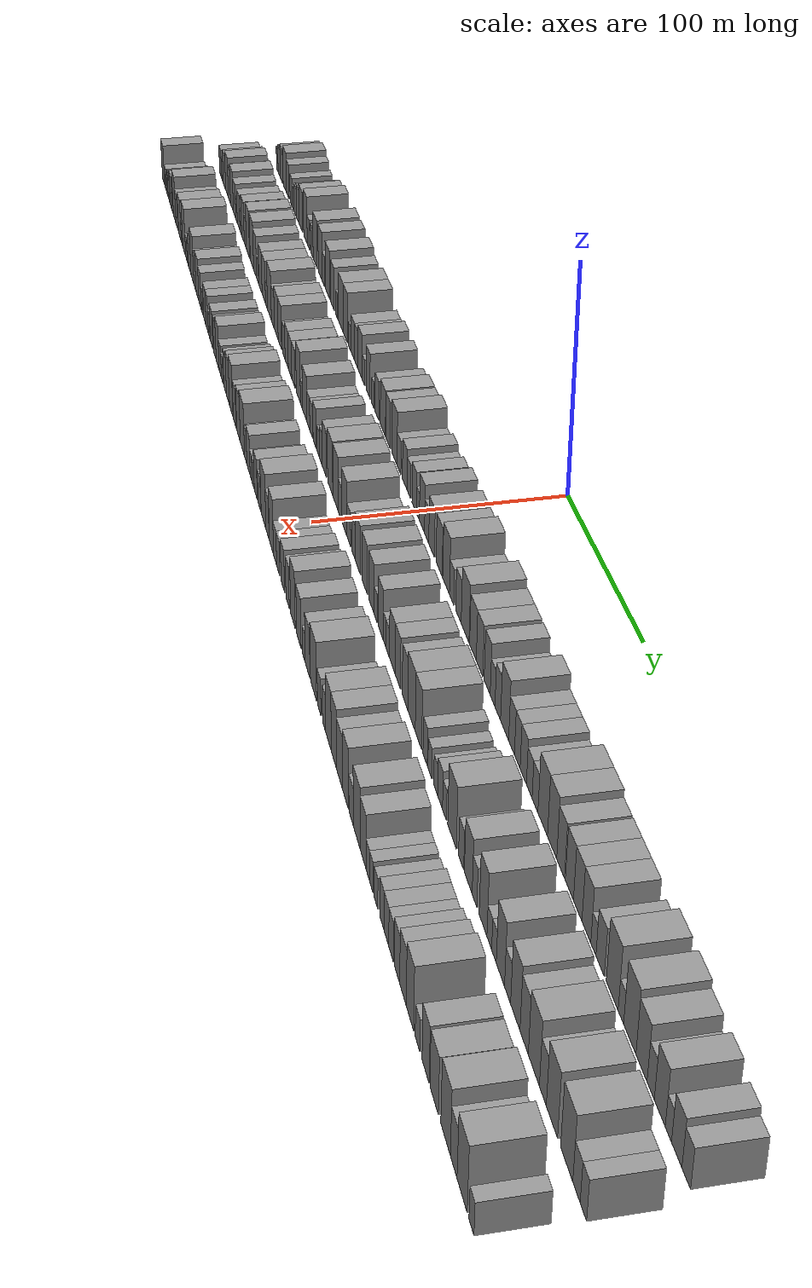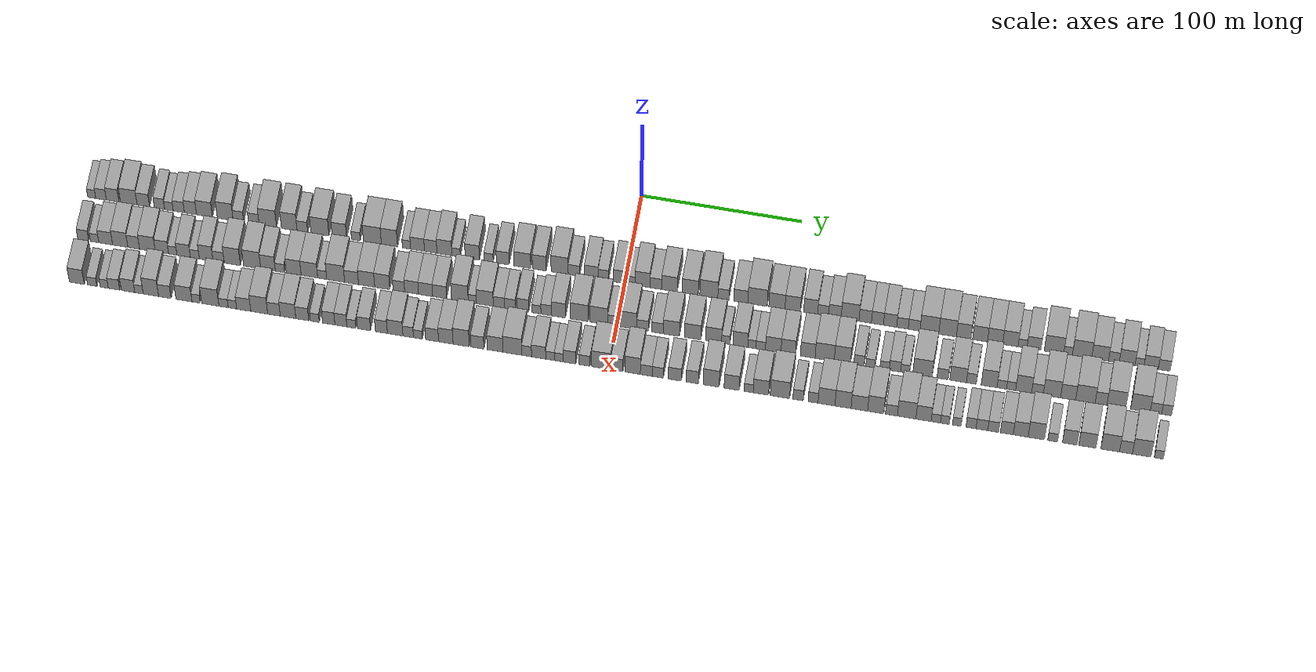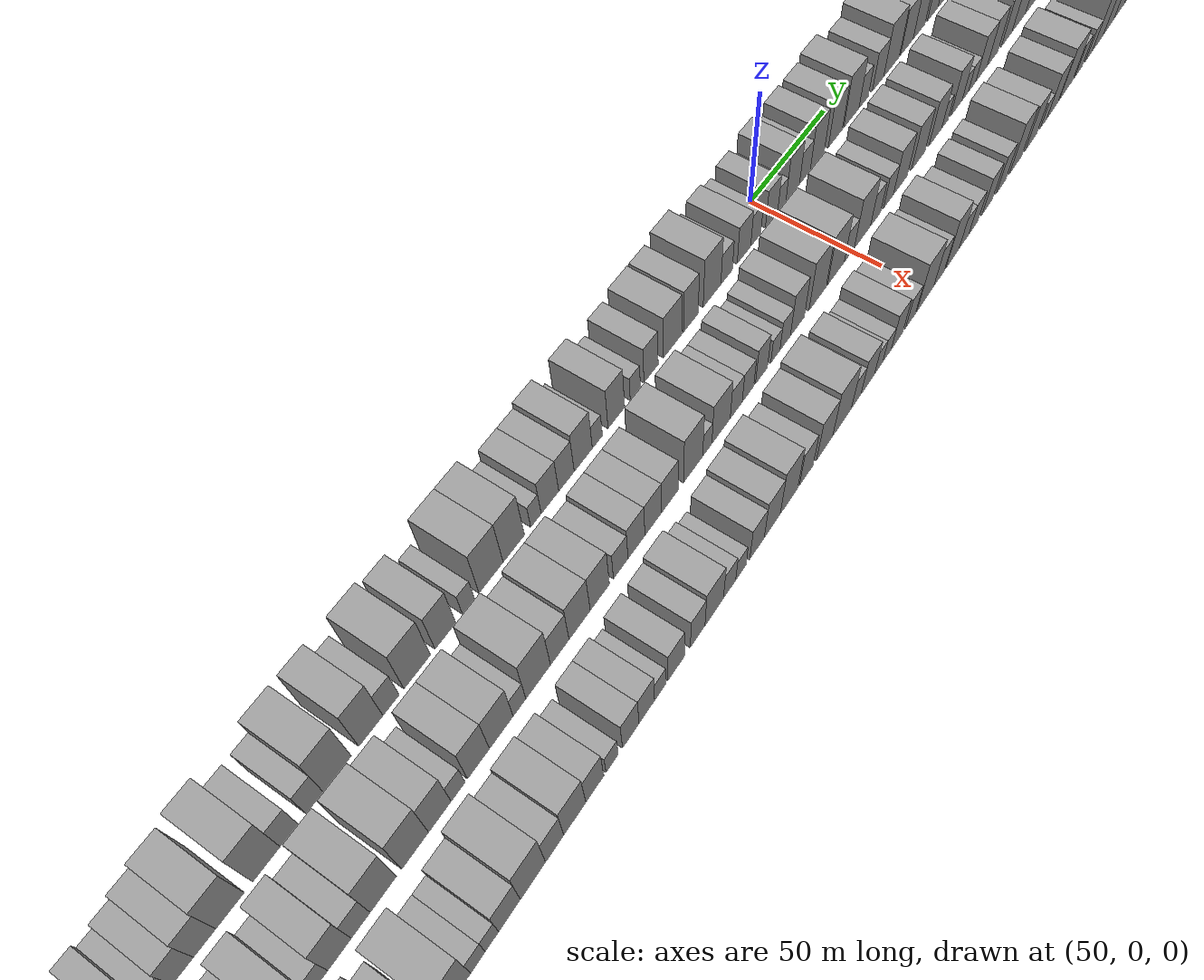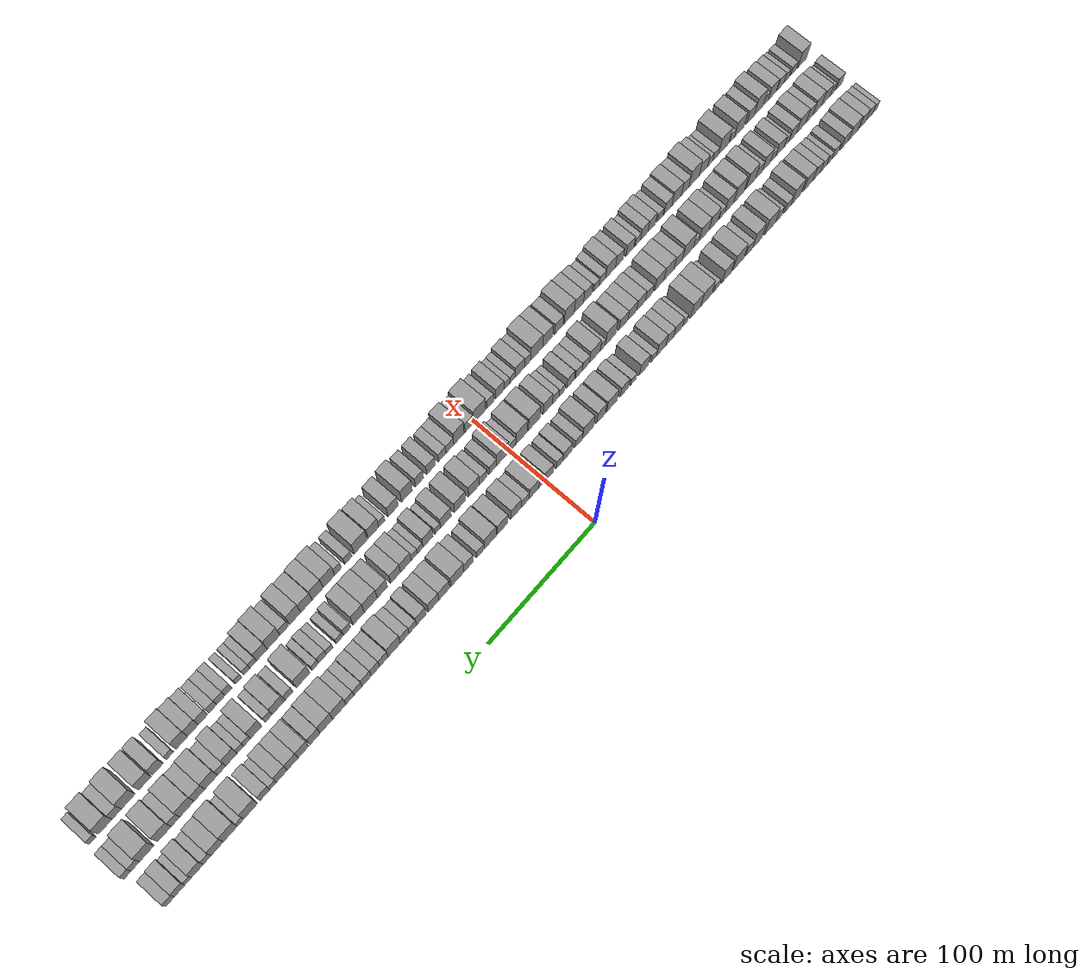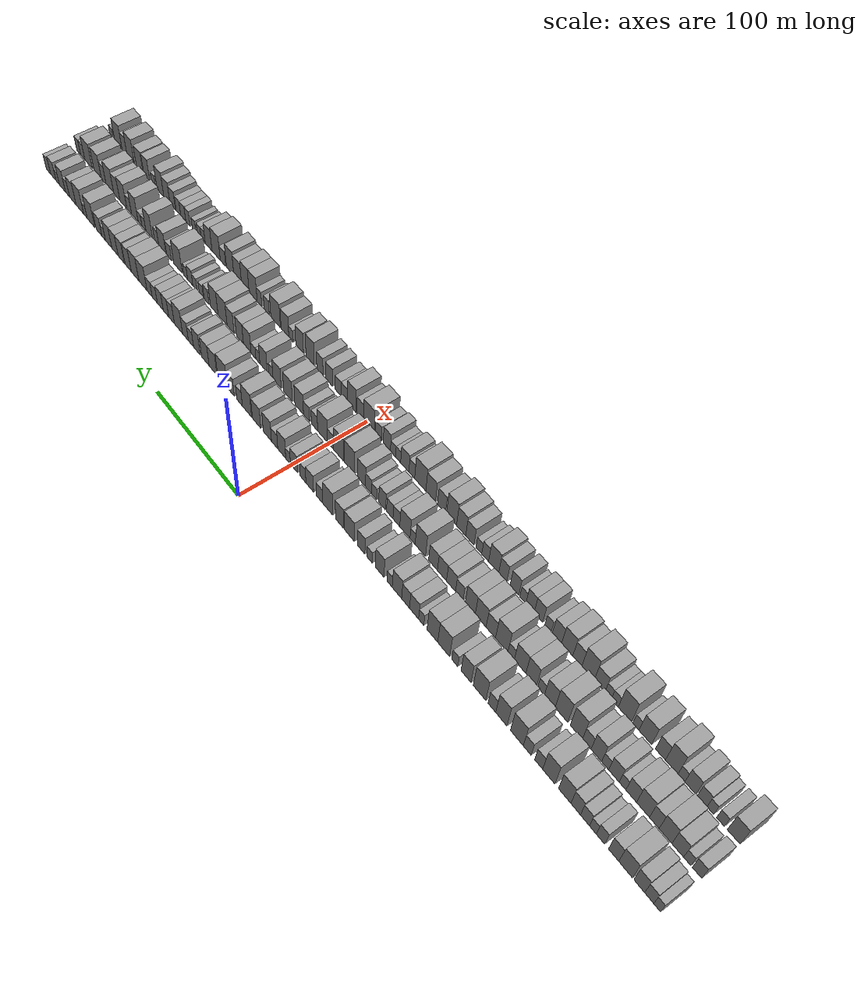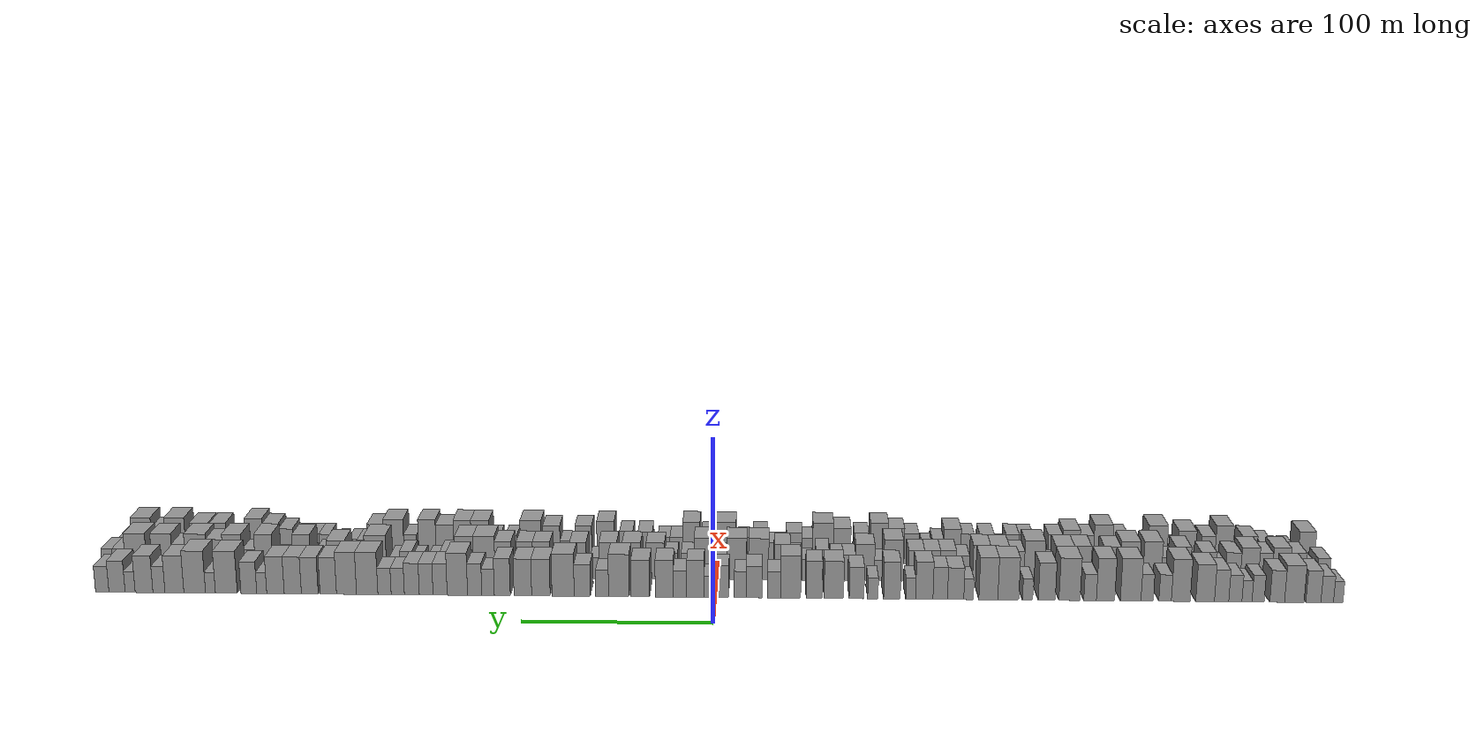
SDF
<sdf version="1.6">
 <world name="default">
  <scene>
   <sky><clouds><speed>12</speed></clouds></sky>
   <ambient>0.4 0.4 0.4 1</ambient>
   <background>0.7 0.7 0.7 1</background>
   <shadows>1</shadows>
  </scene>
  <gravity>0 0 -9.8066</gravity>
  <magnetic_field>6e-06 2.3e-05 -4.2e-05</magnetic_field>
  <physics default="0" name="default_physics" type="ode">
   <ode>
    <solver>
     <type>quick</type>
     <iters>10</iters>
     <sor>1.0</sor>
     <use_dynamic_moi_rescaling>0</use_dynamic_moi_rescaling>
    </solver>
    <constraints>
     <cfm>0</cfm>
     <erp>0.2</erp>
     <contact_max_correcting_vel>100</contact_max_correcting_vel>
     <contact_surface_layer>0.001</contact_surface_layer>
    </constraints>
   </ode>
   <max_step_size>0.004</max_step_size>
   <real_time_factor>1</real_time_factor>
   <real_time_update_rate>250</real_time_update_rate>
  </physics>
  <light name="sun" type="directional">
   <pose>0 0 10 0 0 0</pose>
   <diffuse>0.8 0.8 0.8 1</diffuse>
   <specular>0.2 0.2 0.2 1</specular>
   <attenuation>
    <range>1000</range>
    <constant>0.9</constant>
    <linear>0.01</linear>
    <quadratic>0.001</quadratic>
   </attenuation>
   <direction>-0.5 0.1 -0.9</direction>
  </light>
  <model name="building_1">
   <static>1</static>
   <pose>50.0000 -333.4852 0 0.000000 0.000000 0.000000</pose>
   <link name="link">
    <pose>0 0 6.00 0 0 0</pose>
    <collision name="collision"><geometry><box><size>20.0000 5.0296 12.0000</size></box></geometry></collision>
    <visual name="visual">
     <cast_shadows>0</cast_shadows>
     <geometry><box><size>20.0000 5.0296 12.0000</size></box></geometry>
     <material>
      <script>
       <uri>model://grey_wall/materials/scripts</uri>
       <uri>model://grey_wall/materials/textures</uri>
       <name>vrc/grey_wall</name>
      </script>
     </material>
    </visual>
   </link>
  </model>
  <model name="building_2">
   <static>1</static>
   <pose>50.0000 -327.6248 0 0.000000 0.000000 0.000000</pose>
   <link name="link">
    <pose>0 0 7.50 0 0 0</pose>
    <collision name="collision"><geometry><box><size>20.0000 6.6912 15.0000</size></box></geometry></collision>
    <visual name="visual">
     <cast_shadows>0</cast_shadows>
     <geometry><box><size>20.0000 6.6912 15.0000</size></box></geometry>
     <material>
      <script>
       <uri>model://grey_wall/materials/scripts</uri>
       <uri>model://grey_wall/materials/textures</uri>
       <name>vrc/grey_wall</name>
      </script>
     </material>
    </visual>
   </link>
  </model>
  <model name="building_3">
   <static>1</static>
   <pose>50.0000 -320.2911 0 0.000000 0.000000 0.000000</pose>
   <link name="link">
    <pose>0 0 9.00 0 0 0</pose>
    <collision name="collision"><geometry><box><size>20.0000 7.9762 18.0000</size></box></geometry></collision>
    <visual name="visual">
     <cast_shadows>0</cast_shadows>
     <geometry><box><size>20.0000 7.9762 18.0000</size></box></geometry>
     <material>
      <script>
       <uri>model://grey_wall/materials/scripts</uri>
       <uri>model://grey_wall/materials/textures</uri>
       <name>vrc/grey_wall</name>
      </script>
     </material>
    </visual>
   </link>
  </model>
  <model name="building_4">
   <static>1</static>
   <pose>50.0000 -310.1145 0 0.000000 0.000000 0.000000</pose>
   <link name="link">
    <pose>0 0 10.50 0 0 0</pose>
    <collision name="collision"><geometry><box><size>20.0000 10.3770 21.0000</size></box></geometry></collision>
    <visual name="visual">
     <cast_shadows>0</cast_shadows>
     <geometry><box><size>20.0000 10.3770 21.0000</size></box></geometry>
     <material>
      <script>
       <uri>model://grey_wall/materials/scripts</uri>
       <uri>model://grey_wall/materials/textures</uri>
       <name>vrc/grey_wall</name>
      </script>
     </material>
    </visual>
   </link>
  </model>
  <model name="building_5">
   <static>1</static>
   <pose>50.0000 -301.0032 0 0.000000 0.000000 0.000000</pose>
   <link name="link">
    <pose>0 0 9.00 0 0 0</pose>
    <collision name="collision"><geometry><box><size>20.0000 7.8455 18.0000</size></box></geometry></collision>
    <visual name="visual">
     <cast_shadows>0</cast_shadows>
     <geometry><box><size>20.0000 7.8455 18.0000</size></box></geometry>
     <material>
      <script>
       <uri>model://grey_wall/materials/scripts</uri>
       <uri>model://grey_wall/materials/textures</uri>
       <name>vrc/grey_wall</name>
      </script>
     </material>
    </visual>
   </link>
  </model>
  <model name="building_6">
   <static>1</static>
   <pose>50.0000 -290.8323 0 0.000000 0.000000 0.000000</pose>
   <link name="link">
    <pose>0 0 7.50 0 0 0</pose>
    <collision name="collision"><geometry><box><size>20.0000 6.4964 15.0000</size></box></geometry></collision>
    <visual name="visual">
     <cast_shadows>0</cast_shadows>
     <geometry><box><size>20.0000 6.4964 15.0000</size></box></geometry>
     <material>
      <script>
       <uri>model://grey_wall/materials/scripts</uri>
       <uri>model://grey_wall/materials/textures</uri>
       <name>vrc/grey_wall</name>
      </script>
     </material>
    </visual>
   </link>
  </model>
  <model name="building_7">
   <static>1</static>
   <pose>50.0000 -284.9107 0 0.000000 0.000000 0.000000</pose>
   <link name="link">
    <pose>0 0 6.00 0 0 0</pose>
    <collision name="collision"><geometry><box><size>20.0000 5.3466 12.0000</size></box></geometry></collision>
    <visual name="visual">
     <cast_shadows>0</cast_shadows>
     <geometry><box><size>20.0000 5.3466 12.0000</size></box></geometry>
     <material>
      <script>
       <uri>model://grey_wall/materials/scripts</uri>
       <uri>model://grey_wall/materials/textures</uri>
       <name>vrc/grey_wall</name>
      </script>
     </material>
    </visual>
   </link>
  </model>
  <model name="building_8">
   <static>1</static>
   <pose>50.0000 -278.7191 0 0.000000 0.000000 0.000000</pose>
   <link name="link">
    <pose>0 0 7.50 0 0 0</pose>
    <collision name="collision"><geometry><box><size>20.0000 7.0367 15.0000</size></box></geometry></collision>
    <visual name="visual">
     <cast_shadows>0</cast_shadows>
     <geometry><box><size>20.0000 7.0367 15.0000</size></box></geometry>
     <material>
      <script>
       <uri>model://grey_wall/materials/scripts</uri>
       <uri>model://grey_wall/materials/textures</uri>
       <name>vrc/grey_wall</name>
      </script>
     </material>
    </visual>
   </link>
  </model>
  <model name="building_9">
   <static>1</static>
   <pose>50.0000 -271.3886 0 0.000000 0.000000 0.000000</pose>
   <link name="link">
    <pose>0 0 9.00 0 0 0</pose>
    <collision name="collision"><geometry><box><size>20.0000 7.6242 18.0000</size></box></geometry></collision>
    <visual name="visual">
     <cast_shadows>0</cast_shadows>
     <geometry><box><size>20.0000 7.6242 18.0000</size></box></geometry>
     <material>
      <script>
       <uri>model://grey_wall/materials/scripts</uri>
       <uri>model://grey_wall/materials/textures</uri>
       <name>vrc/grey_wall</name>
      </script>
     </material>
    </visual>
   </link>
  </model>
  <model name="building_10">
   <static>1</static>
   <pose>50.0000 -262.5840 0 0.000000 0.000000 0.000000</pose>
   <link name="link">
    <pose>0 0 10.50 0 0 0</pose>
    <collision name="collision"><geometry><box><size>20.0000 9.9851 21.0000</size></box></geometry></collision>
    <visual name="visual">
     <cast_shadows>0</cast_shadows>
     <geometry><box><size>20.0000 9.9851 21.0000</size></box></geometry>
     <material>
      <script>
       <uri>model://grey_wall/materials/scripts</uri>
       <uri>model://grey_wall/materials/textures</uri>
       <name>vrc/grey_wall</name>
      </script>
     </material>
    </visual>
   </link>
  </model>
  <model name="building_11">
   <static>1</static>
   <pose>50.0000 -249.5773 0 0.000000 0.000000 0.000000</pose>
   <link name="link">
    <pose>0 0 12.00 0 0 0</pose>
    <collision name="collision"><geometry><box><size>20.0000 10.0284 24.0000</size></box></geometry></collision>
    <visual name="visual">
     <cast_shadows>0</cast_shadows>
     <geometry><box><size>20.0000 10.0284 24.0000</size></box></geometry>
     <material>
      <script>
       <uri>model://grey_wall/materials/scripts</uri>
       <uri>model://grey_wall/materials/textures</uri>
       <name>vrc/grey_wall</name>
      </script>
     </material>
    </visual>
   </link>
  </model>
  <model name="building_12">
   <static>1</static>
   <pose>50.0000 -241.2419 0 0.000000 0.000000 0.000000</pose>
   <link name="link">
    <pose>0 0 7.50 0 0 0</pose>
    <collision name="collision"><geometry><box><size>20.0000 6.6423 15.0000</size></box></geometry></collision>
    <visual name="visual">
     <cast_shadows>0</cast_shadows>
     <geometry><box><size>20.0000 6.6423 15.0000</size></box></geometry>
     <material>
      <script>
       <uri>model://grey_wall/materials/scripts</uri>
       <uri>model://grey_wall/materials/textures</uri>
       <name>vrc/grey_wall</name>
      </script>
     </material>
    </visual>
   </link>
  </model>
  <model name="building_13">
   <static>1</static>
   <pose>50.0000 -231.6286 0 0.000000 0.000000 0.000000</pose>
   <link name="link">
    <pose>0 0 7.50 0 0 0</pose>
    <collision name="collision"><geometry><box><size>20.0000 6.5844 15.0000</size></box></geometry></collision>
    <visual name="visual">
     <cast_shadows>0</cast_shadows>
     <geometry><box><size>20.0000 6.5844 15.0000</size></box></geometry>
     <material>
      <script>
       <uri>model://grey_wall/materials/scripts</uri>
       <uri>model://grey_wall/materials/textures</uri>
       <name>vrc/grey_wall</name>
      </script>
     </material>
    </visual>
   </link>
  </model>
  <model name="building_14">
   <static>1</static>
   <pose>50.0000 -222.8365 0 0.000000 0.000000 0.000000</pose>
   <link name="link">
    <pose>0 0 12.00 0 0 0</pose>
    <collision name="collision"><geometry><box><size>20.0000 10.9997 24.0000</size></box></geometry></collision>
    <visual name="visual">
     <cast_shadows>0</cast_shadows>
     <geometry><box><size>20.0000 10.9997 24.0000</size></box></geometry>
     <material>
      <script>
       <uri>model://grey_wall/materials/scripts</uri>
       <uri>model://grey_wall/materials/textures</uri>
       <name>vrc/grey_wall</name>
      </script>
     </material>
    </visual>
   </link>
  </model>
  <model name="building_15">
   <static>1</static>
   <pose>50.0000 -209.4388 0 0.000000 0.000000 0.000000</pose>
   <link name="link">
    <pose>0 0 12.00 0 0 0</pose>
    <collision name="collision"><geometry><box><size>20.0000 9.7958 24.0000</size></box></geometry></collision>
    <visual name="visual">
     <cast_shadows>0</cast_shadows>
     <geometry><box><size>20.0000 9.7958 24.0000</size></box></geometry>
     <material>
      <script>
       <uri>model://grey_wall/materials/scripts</uri>
       <uri>model://grey_wall/materials/textures</uri>
       <name>vrc/grey_wall</name>
      </script>
     </material>
    </visual>
   </link>
  </model>
  <model name="building_16">
   <static>1</static>
   <pose>50.0000 -201.1808 0 0.000000 0.000000 0.000000</pose>
   <link name="link">
    <pose>0 0 7.50 0 0 0</pose>
    <collision name="collision"><geometry><box><size>20.0000 6.7202 15.0000</size></box></geometry></collision>
    <visual name="visual">
     <cast_shadows>0</cast_shadows>
     <geometry><box><size>20.0000 6.7202 15.0000</size></box></geometry>
     <material>
      <script>
       <uri>model://grey_wall/materials/scripts</uri>
       <uri>model://grey_wall/materials/textures</uri>
       <name>vrc/grey_wall</name>
      </script>
     </material>
    </visual>
   </link>
  </model>
  <model name="building_17">
   <static>1</static>
   <pose>50.0000 -190.1766 0 0.000000 0.000000 0.000000</pose>
   <link name="link">
    <pose>0 0 12.00 0 0 0</pose>
    <collision name="collision"><geometry><box><size>20.0000 11.2882 24.0000</size></box></geometry></collision>
    <visual name="visual">
     <cast_shadows>0</cast_shadows>
     <geometry><box><size>20.0000 11.2882 24.0000</size></box></geometry>
     <material>
      <script>
       <uri>model://grey_wall/materials/scripts</uri>
       <uri>model://grey_wall/materials/textures</uri>
       <name>vrc/grey_wall</name>
      </script>
     </material>
    </visual>
   </link>
  </model>
  <model name="building_18">
   <static>1</static>
   <pose>50.0000 -177.9957 0 0.000000 0.000000 0.000000</pose>
   <link name="link">
    <pose>0 0 10.50 0 0 0</pose>
    <collision name="collision"><geometry><box><size>20.0000 9.0736 21.0000</size></box></geometry></collision>
    <visual name="visual">
     <cast_shadows>0</cast_shadows>
     <geometry><box><size>20.0000 9.0736 21.0000</size></box></geometry>
     <material>
      <script>
       <uri>model://grey_wall/materials/scripts</uri>
       <uri>model://grey_wall/materials/textures</uri>
       <name>vrc/grey_wall</name>
      </script>
     </material>
    </visual>
   </link>
  </model>
  <model name="building_19">
   <static>1</static>
   <pose>50.0000 -167.7257 0 0.000000 0.000000 0.000000</pose>
   <link name="link">
    <pose>0 0 6.00 0 0 0</pose>
    <collision name="collision"><geometry><box><size>20.0000 5.4664 12.0000</size></box></geometry></collision>
    <visual name="visual">
     <cast_shadows>0</cast_shadows>
     <geometry><box><size>20.0000 5.4664 12.0000</size></box></geometry>
     <material>
      <script>
       <uri>model://grey_wall/materials/scripts</uri>
       <uri>model://grey_wall/materials/textures</uri>
       <name>vrc/grey_wall</name>
      </script>
     </material>
    </visual>
   </link>
  </model>
  <model name="building_20">
   <static>1</static>
   <pose>50.0000 -157.3953 0 0.000000 0.000000 0.000000</pose>
   <link name="link">
    <pose>0 0 12.00 0 0 0</pose>
    <collision name="collision"><geometry><box><size>20.0000 11.1945 24.0000</size></box></geometry></collision>
    <visual name="visual">
     <cast_shadows>0</cast_shadows>
     <geometry><box><size>20.0000 11.1945 24.0000</size></box></geometry>
     <material>
      <script>
       <uri>model://grey_wall/materials/scripts</uri>
       <uri>model://grey_wall/materials/textures</uri>
       <name>vrc/grey_wall</name>
      </script>
     </material>
    </visual>
   </link>
  </model>
  <model name="building_21">
   <static>1</static>
   <pose>50.0000 -146.7273 0 0.000000 0.000000 0.000000</pose>
   <link name="link">
    <pose>0 0 12.00 0 0 0</pose>
    <collision name="collision"><geometry><box><size>20.0000 10.1413 24.0000</size></box></geometry></collision>
    <visual name="visual">
     <cast_shadows>0</cast_shadows>
     <geometry><box><size>20.0000 10.1413 24.0000</size></box></geometry>
     <material>
      <script>
       <uri>model://grey_wall/materials/scripts</uri>
       <uri>model://grey_wall/materials/textures</uri>
       <name>vrc/grey_wall</name>
      </script>
     </material>
    </visual>
   </link>
  </model>
  <model name="building_22">
   <static>1</static>
   <pose>50.0000 -136.1086 0 0.000000 0.000000 0.000000</pose>
   <link name="link">
    <pose>0 0 6.00 0 0 0</pose>
    <collision name="collision"><geometry><box><size>20.0000 5.0961 12.0000</size></box></geometry></collision>
    <visual name="visual">
     <cast_shadows>0</cast_shadows>
     <geometry><box><size>20.0000 5.0961 12.0000</size></box></geometry>
     <material>
      <script>
       <uri>model://grey_wall/materials/scripts</uri>
       <uri>model://grey_wall/materials/textures</uri>
       <name>vrc/grey_wall</name>
      </script>
     </material>
    </visual>
   </link>
  </model>
  <model name="building_23">
   <static>1</static>
   <pose>50.0000 -129.1905 0 0.000000 0.000000 0.000000</pose>
   <link name="link">
    <pose>0 0 9.00 0 0 0</pose>
    <collision name="collision"><geometry><box><size>20.0000 8.7401 18.0000</size></box></geometry></collision>
    <visual name="visual">
     <cast_shadows>0</cast_shadows>
     <geometry><box><size>20.0000 8.7401 18.0000</size></box></geometry>
     <material>
      <script>
       <uri>model://grey_wall/materials/scripts</uri>
       <uri>model://grey_wall/materials/textures</uri>
       <name>vrc/grey_wall</name>
      </script>
     </material>
    </visual>
   </link>
  </model>
  <model name="building_24">
   <static>1</static>
   <pose>50.0000 -120.9280 0 0.000000 0.000000 0.000000</pose>
   <link name="link">
    <pose>0 0 9.00 0 0 0</pose>
    <collision name="collision"><geometry><box><size>20.0000 7.7850 18.0000</size></box></geometry></collision>
    <visual name="visual">
     <cast_shadows>0</cast_shadows>
     <geometry><box><size>20.0000 7.7850 18.0000</size></box></geometry>
     <material>
      <script>
       <uri>model://grey_wall/materials/scripts</uri>
       <uri>model://grey_wall/materials/textures</uri>
       <name>vrc/grey_wall</name>
      </script>
     </material>
    </visual>
   </link>
  </model>
  <model name="building_25">
   <static>1</static>
   <pose>50.0000 -112.3726 0 0.000000 0.000000 0.000000</pose>
   <link name="link">
    <pose>0 0 10.50 0 0 0</pose>
    <collision name="collision"><geometry><box><size>20.0000 9.3259 21.0000</size></box></geometry></collision>
    <visual name="visual">
     <cast_shadows>0</cast_shadows>
     <geometry><box><size>20.0000 9.3259 21.0000</size></box></geometry>
     <material>
      <script>
       <uri>model://grey_wall/materials/scripts</uri>
       <uri>model://grey_wall/materials/textures</uri>
       <name>vrc/grey_wall</name>
      </script>
     </material>
    </visual>
   </link>
  </model>
  <model name="building_26">
   <static>1</static>
   <pose>50.0000 -105.0843 0 0.000000 0.000000 0.000000</pose>
   <link name="link">
    <pose>0 0 6.00 0 0 0</pose>
    <collision name="collision"><geometry><box><size>20.0000 5.2507 12.0000</size></box></geometry></collision>
    <visual name="visual">
     <cast_shadows>0</cast_shadows>
     <geometry><box><size>20.0000 5.2507 12.0000</size></box></geometry>
     <material>
      <script>
       <uri>model://grey_wall/materials/scripts</uri>
       <uri>model://grey_wall/materials/textures</uri>
       <name>vrc/grey_wall</name>
      </script>
     </material>
    </visual>
   </link>
  </model>
  <model name="building_27">
   <static>1</static>
   <pose>50.0000 -95.0004 0 0.000000 0.000000 0.000000</pose>
   <link name="link">
    <pose>0 0 10.50 0 0 0</pose>
    <collision name="collision"><geometry><box><size>20.0000 8.9172 21.0000</size></box></geometry></collision>
    <visual name="visual">
     <cast_shadows>0</cast_shadows>
     <geometry><box><size>20.0000 8.9172 21.0000</size></box></geometry>
     <material>
      <script>
       <uri>model://grey_wall/materials/scripts</uri>
       <uri>model://grey_wall/materials/textures</uri>
       <name>vrc/grey_wall</name>
      </script>
     </material>
    </visual>
   </link>
  </model>
  <model name="building_28">
   <static>1</static>
   <pose>50.0000 -84.7550 0 0.000000 0.000000 0.000000</pose>
   <link name="link">
    <pose>0 0 6.00 0 0 0</pose>
    <collision name="collision"><geometry><box><size>20.0000 5.5736 12.0000</size></box></geometry></collision>
    <visual name="visual">
     <cast_shadows>0</cast_shadows>
     <geometry><box><size>20.0000 5.5736 12.0000</size></box></geometry>
     <material>
      <script>
       <uri>model://grey_wall/materials/scripts</uri>
       <uri>model://grey_wall/materials/textures</uri>
       <name>vrc/grey_wall</name>
      </script>
     </material>
    </visual>
   </link>
  </model>
  <model name="building_29">
   <static>1</static>
   <pose>50.0000 -76.0003 0 0.000000 0.000000 0.000000</pose>
   <link name="link">
    <pose>0 0 9.00 0 0 0</pose>
    <collision name="collision"><geometry><box><size>20.0000 7.9358 18.0000</size></box></geometry></collision>
    <visual name="visual">
     <cast_shadows>0</cast_shadows>
     <geometry><box><size>20.0000 7.9358 18.0000</size></box></geometry>
     <material>
      <script>
       <uri>model://grey_wall/materials/scripts</uri>
       <uri>model://grey_wall/materials/textures</uri>
       <name>vrc/grey_wall</name>
      </script>
     </material>
    </visual>
   </link>
  </model>
  <model name="building_30">
   <static>1</static>
   <pose>50.0000 -63.7899 0 0.000000 0.000000 0.000000</pose>
   <link name="link">
    <pose>0 0 10.50 0 0 0</pose>
    <collision name="collision"><geometry><box><size>20.0000 10.4850 21.0000</size></box></geometry></collision>
    <visual name="visual">
     <cast_shadows>0</cast_shadows>
     <geometry><box><size>20.0000 10.4850 21.0000</size></box></geometry>
     <material>
      <script>
       <uri>model://grey_wall/materials/scripts</uri>
       <uri>model://grey_wall/materials/textures</uri>
       <name>vrc/grey_wall</name>
      </script>
     </material>
    </visual>
   </link>
  </model>
  <model name="building_31">
   <static>1</static>
   <pose>50.0000 -53.2239 0 0.000000 0.000000 0.000000</pose>
   <link name="link">
    <pose>0 0 10.50 0 0 0</pose>
    <collision name="collision"><geometry><box><size>20.0000 8.6469 21.0000</size></box></geometry></collision>
    <visual name="visual">
     <cast_shadows>0</cast_shadows>
     <geometry><box><size>20.0000 8.6469 21.0000</size></box></geometry>
     <material>
      <script>
       <uri>model://grey_wall/materials/scripts</uri>
       <uri>model://grey_wall/materials/textures</uri>
       <name>vrc/grey_wall</name>
      </script>
     </material>
    </visual>
   </link>
  </model>
  <model name="building_32">
   <static>1</static>
   <pose>50.0000 -40.5641 0 0.000000 0.000000 0.000000</pose>
   <link name="link">
    <pose>0 0 12.00 0 0 0</pose>
    <collision name="collision"><geometry><box><size>20.0000 10.6726 24.0000</size></box></geometry></collision>
    <visual name="visual">
     <cast_shadows>0</cast_shadows>
     <geometry><box><size>20.0000 10.6726 24.0000</size></box></geometry>
     <material>
      <script>
       <uri>model://grey_wall/materials/scripts</uri>
       <uri>model://grey_wall/materials/textures</uri>
       <name>vrc/grey_wall</name>
      </script>
     </material>
    </visual>
   </link>
  </model>
  <model name="building_33">
   <static>1</static>
   <pose>50.0000 -31.6713 0 0.000000 0.000000 0.000000</pose>
   <link name="link">
    <pose>0 0 7.50 0 0 0</pose>
    <collision name="collision"><geometry><box><size>20.0000 7.1129 15.0000</size></box></geometry></collision>
    <visual name="visual">
     <cast_shadows>0</cast_shadows>
     <geometry><box><size>20.0000 7.1129 15.0000</size></box></geometry>
     <material>
      <script>
       <uri>model://grey_wall/materials/scripts</uri>
       <uri>model://grey_wall/materials/textures</uri>
       <name>vrc/grey_wall</name>
      </script>
     </material>
    </visual>
   </link>
  </model>
  <model name="building_34">
   <static>1</static>
   <pose>50.0000 -20.8521 0 0.000000 0.000000 0.000000</pose>
   <link name="link">
    <pose>0 0 9.00 0 0 0</pose>
    <collision name="collision"><geometry><box><size>20.0000 8.5255 18.0000</size></box></geometry></collision>
    <visual name="visual">
     <cast_shadows>0</cast_shadows>
     <geometry><box><size>20.0000 8.5255 18.0000</size></box></geometry>
     <material>
      <script>
       <uri>model://grey_wall/materials/scripts</uri>
       <uri>model://grey_wall/materials/textures</uri>
       <name>vrc/grey_wall</name>
      </script>
     </material>
    </visual>
   </link>
  </model>
  <model name="building_35">
   <static>1</static>
   <pose>50.0000 -13.3748 0 0.000000 0.000000 0.000000</pose>
   <link name="link">
    <pose>0 0 7.50 0 0 0</pose>
    <collision name="collision"><geometry><box><size>20.0000 6.4291 15.0000</size></box></geometry></collision>
    <visual name="visual">
     <cast_shadows>0</cast_shadows>
     <geometry><box><size>20.0000 6.4291 15.0000</size></box></geometry>
     <material>
      <script>
       <uri>model://grey_wall/materials/scripts</uri>
       <uri>model://grey_wall/materials/textures</uri>
       <name>vrc/grey_wall</name>
      </script>
     </material>
    </visual>
   </link>
  </model>
  <model name="building_36">
   <static>1</static>
   <pose>50.0000 -3.1231 0 0.000000 0.000000 0.000000</pose>
   <link name="link">
    <pose>0 0 9.00 0 0 0</pose>
    <collision name="collision"><geometry><box><size>20.0000 8.0743 18.0000</size></box></geometry></collision>
    <visual name="visual">
     <cast_shadows>0</cast_shadows>
     <geometry><box><size>20.0000 8.0743 18.0000</size></box></geometry>
     <material>
      <script>
       <uri>model://grey_wall/materials/scripts</uri>
       <uri>model://grey_wall/materials/textures</uri>
       <name>vrc/grey_wall</name>
      </script>
     </material>
    </visual>
   </link>
  </model>
  <model name="building_37">
   <static>1</static>
   <pose>50.0000 3.6202 0 0.000000 0.000000 0.000000</pose>
   <link name="link">
    <pose>0 0 6.00 0 0 0</pose>
    <collision name="collision"><geometry><box><size>20.0000 5.4123 12.0000</size></box></geometry></collision>
    <visual name="visual">
     <cast_shadows>0</cast_shadows>
     <geometry><box><size>20.0000 5.4123 12.0000</size></box></geometry>
     <material>
      <script>
       <uri>model://grey_wall/materials/scripts</uri>
       <uri>model://grey_wall/materials/textures</uri>
       <name>vrc/grey_wall</name>
      </script>
     </material>
    </visual>
   </link>
  </model>
  <model name="building_38">
   <static>1</static>
   <pose>50.0000 10.9065 0 0.000000 0.000000 0.000000</pose>
   <link name="link">
    <pose>0 0 10.50 0 0 0</pose>
    <collision name="collision"><geometry><box><size>20.0000 9.1602 21.0000</size></box></geometry></collision>
    <visual name="visual">
     <cast_shadows>0</cast_shadows>
     <geometry><box><size>20.0000 9.1602 21.0000</size></box></geometry>
     <material>
      <script>
       <uri>model://grey_wall/materials/scripts</uri>
       <uri>model://grey_wall/materials/textures</uri>
       <name>vrc/grey_wall</name>
      </script>
     </material>
    </visual>
   </link>
  </model>
  <model name="building_39">
   <static>1</static>
   <pose>50.0000 19.1723 0 0.000000 0.000000 0.000000</pose>
   <link name="link">
    <pose>0 0 7.50 0 0 0</pose>
    <collision name="collision"><geometry><box><size>20.0000 7.3716 15.0000</size></box></geometry></collision>
    <visual name="visual">
     <cast_shadows>0</cast_shadows>
     <geometry><box><size>20.0000 7.3716 15.0000</size></box></geometry>
     <material>
      <script>
       <uri>model://grey_wall/materials/scripts</uri>
       <uri>model://grey_wall/materials/textures</uri>
       <name>vrc/grey_wall</name>
      </script>
     </material>
    </visual>
   </link>
  </model>
  <model name="building_40">
   <static>1</static>
   <pose>50.0000 27.6833 0 0.000000 0.000000 0.000000</pose>
   <link name="link">
    <pose>0 0 10.50 0 0 0</pose>
    <collision name="collision"><geometry><box><size>20.0000 9.6505 21.0000</size></box></geometry></collision>
    <visual name="visual">
     <cast_shadows>0</cast_shadows>
     <geometry><box><size>20.0000 9.6505 21.0000</size></box></geometry>
     <material>
      <script>
       <uri>model://grey_wall/materials/scripts</uri>
       <uri>model://grey_wall/materials/textures</uri>
       <name>vrc/grey_wall</name>
      </script>
     </material>
    </visual>
   </link>
  </model>
  <model name="building_41">
   <static>1</static>
   <pose>50.0000 40.5229 0 0.000000 0.000000 0.000000</pose>
   <link name="link">
    <pose>0 0 10.50 0 0 0</pose>
    <collision name="collision"><geometry><box><size>20.0000 10.0286 21.0000</size></box></geometry></collision>
    <visual name="visual">
     <cast_shadows>0</cast_shadows>
     <geometry><box><size>20.0000 10.0286 21.0000</size></box></geometry>
     <material>
      <script>
       <uri>model://grey_wall/materials/scripts</uri>
       <uri>model://grey_wall/materials/textures</uri>
       <name>vrc/grey_wall</name>
      </script>
     </material>
    </visual>
   </link>
  </model>
  <model name="building_42">
   <static>1</static>
   <pose>50.0000 52.1175 0 0.000000 0.000000 0.000000</pose>
   <link name="link">
    <pose>0 0 12.00 0 0 0</pose>
    <collision name="collision"><geometry><box><size>20.0000 11.1605 24.0000</size></box></geometry></collision>
    <visual name="visual">
     <cast_shadows>0</cast_shadows>
     <geometry><box><size>20.0000 11.1605 24.0000</size></box></geometry>
     <material>
      <script>
       <uri>model://grey_wall/materials/scripts</uri>
       <uri>model://grey_wall/materials/textures</uri>
       <name>vrc/grey_wall</name>
      </script>
     </material>
    </visual>
   </link>
  </model>
  <model name="building_43">
   <static>1</static>
   <pose>50.0000 61.1366 0 0.000000 0.000000 0.000000</pose>
   <link name="link">
    <pose>0 0 7.50 0 0 0</pose>
    <collision name="collision"><geometry><box><size>20.0000 6.8779 15.0000</size></box></geometry></collision>
    <visual name="visual">
     <cast_shadows>0</cast_shadows>
     <geometry><box><size>20.0000 6.8779 15.0000</size></box></geometry>
     <material>
      <script>
       <uri>model://grey_wall/materials/scripts</uri>
       <uri>model://grey_wall/materials/textures</uri>
       <name>vrc/grey_wall</name>
      </script>
     </material>
    </visual>
   </link>
  </model>
  <model name="building_44">
   <static>1</static>
   <pose>50.0000 71.9413 0 0.000000 0.000000 0.000000</pose>
   <link name="link">
    <pose>0 0 9.00 0 0 0</pose>
    <collision name="collision"><geometry><box><size>20.0000 8.7314 18.0000</size></box></geometry></collision>
    <visual name="visual">
     <cast_shadows>0</cast_shadows>
     <geometry><box><size>20.0000 8.7314 18.0000</size></box></geometry>
     <material>
      <script>
       <uri>model://grey_wall/materials/scripts</uri>
       <uri>model://grey_wall/materials/textures</uri>
       <name>vrc/grey_wall</name>
      </script>
     </material>
    </visual>
   </link>
  </model>
  <model name="building_45">
   <static>1</static>
   <pose>50.0000 82.3066 0 0.000000 0.000000 0.000000</pose>
   <link name="link">
    <pose>0 0 12.00 0 0 0</pose>
    <collision name="collision"><geometry><box><size>20.0000 11.9993 24.0000</size></box></geometry></collision>
    <visual name="visual">
     <cast_shadows>0</cast_shadows>
     <geometry><box><size>20.0000 11.9993 24.0000</size></box></geometry>
     <material>
      <script>
       <uri>model://grey_wall/materials/scripts</uri>
       <uri>model://grey_wall/materials/textures</uri>
       <name>vrc/grey_wall</name>
      </script>
     </material>
    </visual>
   </link>
  </model>
  <model name="building_46">
   <static>1</static>
   <pose>50.0000 94.3098 0 0.000000 0.000000 0.000000</pose>
   <link name="link">
    <pose>0 0 10.50 0 0 0</pose>
    <collision name="collision"><geometry><box><size>20.0000 10.0070 21.0000</size></box></geometry></collision>
    <visual name="visual">
     <cast_shadows>0</cast_shadows>
     <geometry><box><size>20.0000 10.0070 21.0000</size></box></geometry>
     <material>
      <script>
       <uri>model://grey_wall/materials/scripts</uri>
       <uri>model://grey_wall/materials/textures</uri>
       <name>vrc/grey_wall</name>
      </script>
     </material>
    </visual>
   </link>
  </model>
  <model name="building_47">
   <static>1</static>
   <pose>50.0000 104.0893 0 0.000000 0.000000 0.000000</pose>
   <link name="link">
    <pose>0 0 10.50 0 0 0</pose>
    <collision name="collision"><geometry><box><size>20.0000 9.5521 21.0000</size></box></geometry></collision>
    <visual name="visual">
     <cast_shadows>0</cast_shadows>
     <geometry><box><size>20.0000 9.5521 21.0000</size></box></geometry>
     <material>
      <script>
       <uri>model://grey_wall/materials/scripts</uri>
       <uri>model://grey_wall/materials/textures</uri>
       <name>vrc/grey_wall</name>
      </script>
     </material>
    </visual>
   </link>
  </model>
  <model name="building_48">
   <static>1</static>
   <pose>50.0000 115.2018 0 0.000000 0.000000 0.000000</pose>
   <link name="link">
    <pose>0 0 10.50 0 0 0</pose>
    <collision name="collision"><geometry><box><size>20.0000 8.6728 21.0000</size></box></geometry></collision>
    <visual name="visual">
     <cast_shadows>0</cast_shadows>
     <geometry><box><size>20.0000 8.6728 21.0000</size></box></geometry>
     <material>
      <script>
       <uri>model://grey_wall/materials/scripts</uri>
       <uri>model://grey_wall/materials/textures</uri>
       <name>vrc/grey_wall</name>
      </script>
     </material>
    </visual>
   </link>
  </model>
  <model name="building_49">
   <static>1</static>
   <pose>50.0000 122.9129 0 0.000000 0.000000 0.000000</pose>
   <link name="link">
    <pose>0 0 7.50 0 0 0</pose>
    <collision name="collision"><geometry><box><size>20.0000 6.7494 15.0000</size></box></geometry></collision>
    <visual name="visual">
     <cast_shadows>0</cast_shadows>
     <geometry><box><size>20.0000 6.7494 15.0000</size></box></geometry>
     <material>
      <script>
       <uri>model://grey_wall/materials/scripts</uri>
       <uri>model://grey_wall/materials/textures</uri>
       <name>vrc/grey_wall</name>
      </script>
     </material>
    </visual>
   </link>
  </model>
  <model name="building_50">
   <static>1</static>
   <pose>50.0000 130.1622 0 0.000000 0.000000 0.000000</pose>
   <link name="link">
    <pose>0 0 9.00 0 0 0</pose>
    <collision name="collision"><geometry><box><size>20.0000 7.7492 18.0000</size></box></geometry></collision>
    <visual name="visual">
     <cast_shadows>0</cast_shadows>
     <geometry><box><size>20.0000 7.7492 18.0000</size></box></geometry>
     <material>
      <script>
       <uri>model://grey_wall/materials/scripts</uri>
       <uri>model://grey_wall/materials/textures</uri>
       <name>vrc/grey_wall</name>
      </script>
     </material>
    </visual>
   </link>
  </model>
  <model name="building_51">
   <static>1</static>
   <pose>50.0000 139.5643 0 0.000000 0.000000 0.000000</pose>
   <link name="link">
    <pose>0 0 12.00 0 0 0</pose>
    <collision name="collision"><geometry><box><size>20.0000 11.0550 24.0000</size></box></geometry></collision>
    <visual name="visual">
     <cast_shadows>0</cast_shadows>
     <geometry><box><size>20.0000 11.0550 24.0000</size></box></geometry>
     <material>
      <script>
       <uri>model://grey_wall/materials/scripts</uri>
       <uri>model://grey_wall/materials/textures</uri>
       <name>vrc/grey_wall</name>
      </script>
     </material>
    </visual>
   </link>
  </model>
  <model name="building_52">
   <static>1</static>
   <pose>50.0000 148.9306 0 0.000000 0.000000 0.000000</pose>
   <link name="link">
    <pose>0 0 9.00 0 0 0</pose>
    <collision name="collision"><geometry><box><size>20.0000 7.6774 18.0000</size></box></geometry></collision>
    <visual name="visual">
     <cast_shadows>0</cast_shadows>
     <geometry><box><size>20.0000 7.6774 18.0000</size></box></geometry>
     <material>
      <script>
       <uri>model://grey_wall/materials/scripts</uri>
       <uri>model://grey_wall/materials/textures</uri>
       <name>vrc/grey_wall</name>
      </script>
     </material>
    </visual>
   </link>
  </model>
  <model name="building_53">
   <static>1</static>
   <pose>50.0000 156.5016 0 0.000000 0.000000 0.000000</pose>
   <link name="link">
    <pose>0 0 9.00 0 0 0</pose>
    <collision name="collision"><geometry><box><size>20.0000 7.4646 18.0000</size></box></geometry></collision>
    <visual name="visual">
     <cast_shadows>0</cast_shadows>
     <geometry><box><size>20.0000 7.4646 18.0000</size></box></geometry>
     <material>
      <script>
       <uri>model://grey_wall/materials/scripts</uri>
       <uri>model://grey_wall/materials/textures</uri>
       <name>vrc/grey_wall</name>
      </script>
     </material>
    </visual>
   </link>
  </model>
  <model name="building_54">
   <static>1</static>
   <pose>50.0000 164.2882 0 0.000000 0.000000 0.000000</pose>
   <link name="link">
    <pose>0 0 9.00 0 0 0</pose>
    <collision name="collision"><geometry><box><size>20.0000 8.1086 18.0000</size></box></geometry></collision>
    <visual name="visual">
     <cast_shadows>0</cast_shadows>
     <geometry><box><size>20.0000 8.1086 18.0000</size></box></geometry>
     <material>
      <script>
       <uri>model://grey_wall/materials/scripts</uri>
       <uri>model://grey_wall/materials/textures</uri>
       <name>vrc/grey_wall</name>
      </script>
     </material>
    </visual>
   </link>
  </model>
  <model name="building_55">
   <static>1</static>
   <pose>50.0000 171.9306 0 0.000000 0.000000 0.000000</pose>
   <link name="link">
    <pose>0 0 7.50 0 0 0</pose>
    <collision name="collision"><geometry><box><size>20.0000 7.1762 15.0000</size></box></geometry></collision>
    <visual name="visual">
     <cast_shadows>0</cast_shadows>
     <geometry><box><size>20.0000 7.1762 15.0000</size></box></geometry>
     <material>
      <script>
       <uri>model://grey_wall/materials/scripts</uri>
       <uri>model://grey_wall/materials/textures</uri>
       <name>vrc/grey_wall</name>
      </script>
     </material>
    </visual>
   </link>
  </model>
  <model name="building_56">
   <static>1</static>
   <pose>50.0000 179.1338 0 0.000000 0.000000 0.000000</pose>
   <link name="link">
    <pose>0 0 7.50 0 0 0</pose>
    <collision name="collision"><geometry><box><size>20.0000 7.2301 15.0000</size></box></geometry></collision>
    <visual name="visual">
     <cast_shadows>0</cast_shadows>
     <geometry><box><size>20.0000 7.2301 15.0000</size></box></geometry>
     <material>
      <script>
       <uri>model://grey_wall/materials/scripts</uri>
       <uri>model://grey_wall/materials/textures</uri>
       <name>vrc/grey_wall</name>
      </script>
     </material>
    </visual>
   </link>
  </model>
  <model name="building_57">
   <static>1</static>
   <pose>50.0000 188.5393 0 0.000000 0.000000 0.000000</pose>
   <link name="link">
    <pose>0 0 12.00 0 0 0</pose>
    <collision name="collision"><geometry><box><size>20.0000 11.5809 24.0000</size></box></geometry></collision>
    <visual name="visual">
     <cast_shadows>0</cast_shadows>
     <geometry><box><size>20.0000 11.5809 24.0000</size></box></geometry>
     <material>
      <script>
       <uri>model://grey_wall/materials/scripts</uri>
       <uri>model://grey_wall/materials/textures</uri>
       <name>vrc/grey_wall</name>
      </script>
     </material>
    </visual>
   </link>
  </model>
  <model name="building_58">
   <static>1</static>
   <pose>50.0000 199.7946 0 0.000000 0.000000 0.000000</pose>
   <link name="link">
    <pose>0 0 12.00 0 0 0</pose>
    <collision name="collision"><geometry><box><size>20.0000 10.9297 24.0000</size></box></geometry></collision>
    <visual name="visual">
     <cast_shadows>0</cast_shadows>
     <geometry><box><size>20.0000 10.9297 24.0000</size></box></geometry>
     <material>
      <script>
       <uri>model://grey_wall/materials/scripts</uri>
       <uri>model://grey_wall/materials/textures</uri>
       <name>vrc/grey_wall</name>
      </script>
     </material>
    </visual>
   </link>
  </model>
  <model name="building_59">
   <static>1</static>
   <pose>50.0000 209.7275 0 0.000000 0.000000 0.000000</pose>
   <link name="link">
    <pose>0 0 10.50 0 0 0</pose>
    <collision name="collision"><geometry><box><size>20.0000 8.9361 21.0000</size></box></geometry></collision>
    <visual name="visual">
     <cast_shadows>0</cast_shadows>
     <geometry><box><size>20.0000 8.9361 21.0000</size></box></geometry>
     <material>
      <script>
       <uri>model://grey_wall/materials/scripts</uri>
       <uri>model://grey_wall/materials/textures</uri>
       <name>vrc/grey_wall</name>
      </script>
     </material>
    </visual>
   </link>
  </model>
  <model name="building_60">
   <static>1</static>
   <pose>50.0000 219.7772 0 0.000000 0.000000 0.000000</pose>
   <link name="link">
    <pose>0 0 10.50 0 0 0</pose>
    <collision name="collision"><geometry><box><size>20.0000 9.1634 21.0000</size></box></geometry></collision>
    <visual name="visual">
     <cast_shadows>0</cast_shadows>
     <geometry><box><size>20.0000 9.1634 21.0000</size></box></geometry>
     <material>
      <script>
       <uri>model://grey_wall/materials/scripts</uri>
       <uri>model://grey_wall/materials/textures</uri>
       <name>vrc/grey_wall</name>
      </script>
     </material>
    </visual>
   </link>
  </model>
  <model name="building_61">
   <static>1</static>
   <pose>50.0000 229.0346 0 0.000000 0.000000 0.000000</pose>
   <link name="link">
    <pose>0 0 10.50 0 0 0</pose>
    <collision name="collision"><geometry><box><size>20.0000 9.3516 21.0000</size></box></geometry></collision>
    <visual name="visual">
     <cast_shadows>0</cast_shadows>
     <geometry><box><size>20.0000 9.3516 21.0000</size></box></geometry>
     <material>
      <script>
       <uri>model://grey_wall/materials/scripts</uri>
       <uri>model://grey_wall/materials/textures</uri>
       <name>vrc/grey_wall</name>
      </script>
     </material>
    </visual>
   </link>
  </model>
  <model name="building_62">
   <static>1</static>
   <pose>50.0000 238.4718 0 0.000000 0.000000 0.000000</pose>
   <link name="link">
    <pose>0 0 10.50 0 0 0</pose>
    <collision name="collision"><geometry><box><size>20.0000 9.5228 21.0000</size></box></geometry></collision>
    <visual name="visual">
     <cast_shadows>0</cast_shadows>
     <geometry><box><size>20.0000 9.5228 21.0000</size></box></geometry>
     <material>
      <script>
       <uri>model://grey_wall/materials/scripts</uri>
       <uri>model://grey_wall/materials/textures</uri>
       <name>vrc/grey_wall</name>
      </script>
     </material>
    </visual>
   </link>
  </model>
  <model name="building_63">
   <static>1</static>
   <pose>50.0000 245.9495 0 0.000000 0.000000 0.000000</pose>
   <link name="link">
    <pose>0 0 6.00 0 0 0</pose>
    <collision name="collision"><geometry><box><size>20.0000 5.4326 12.0000</size></box></geometry></collision>
    <visual name="visual">
     <cast_shadows>0</cast_shadows>
     <geometry><box><size>20.0000 5.4326 12.0000</size></box></geometry>
     <material>
      <script>
       <uri>model://grey_wall/materials/scripts</uri>
       <uri>model://grey_wall/materials/textures</uri>
       <name>vrc/grey_wall</name>
      </script>
     </material>
    </visual>
   </link>
  </model>
  <model name="building_64">
   <static>1</static>
   <pose>50.0000 252.9692 0 0.000000 0.000000 0.000000</pose>
   <link name="link">
    <pose>0 0 9.00 0 0 0</pose>
    <collision name="collision"><geometry><box><size>20.0000 8.6067 18.0000</size></box></geometry></collision>
    <visual name="visual">
     <cast_shadows>0</cast_shadows>
     <geometry><box><size>20.0000 8.6067 18.0000</size></box></geometry>
     <material>
      <script>
       <uri>model://grey_wall/materials/scripts</uri>
       <uri>model://grey_wall/materials/textures</uri>
       <name>vrc/grey_wall</name>
      </script>
     </material>
    </visual>
   </link>
  </model>
  <model name="building_65">
   <static>1</static>
   <pose>50.0000 265.2506 0 0.000000 0.000000 0.000000</pose>
   <link name="link">
    <pose>0 0 12.00 0 0 0</pose>
    <collision name="collision"><geometry><box><size>20.0000 11.9563 24.0000</size></box></geometry></collision>
    <visual name="visual">
     <cast_shadows>0</cast_shadows>
     <geometry><box><size>20.0000 11.9563 24.0000</size></box></geometry>
     <material>
      <script>
       <uri>model://grey_wall/materials/scripts</uri>
       <uri>model://grey_wall/materials/textures</uri>
       <name>vrc/grey_wall</name>
      </script>
     </material>
    </visual>
   </link>
  </model>
  <model name="building_66">
   <static>1</static>
   <pose>50.0000 273.9183 0 0.000000 0.000000 0.000000</pose>
   <link name="link">
    <pose>0 0 6.00 0 0 0</pose>
    <collision name="collision"><geometry><box><size>20.0000 5.3791 12.0000</size></box></geometry></collision>
    <visual name="visual">
     <cast_shadows>0</cast_shadows>
     <geometry><box><size>20.0000 5.3791 12.0000</size></box></geometry>
     <material>
      <script>
       <uri>model://grey_wall/materials/scripts</uri>
       <uri>model://grey_wall/materials/textures</uri>
       <name>vrc/grey_wall</name>
      </script>
     </material>
    </visual>
   </link>
  </model>
  <model name="building_67">
   <static>1</static>
   <pose>50.0000 282.5137 0 0.000000 0.000000 0.000000</pose>
   <link name="link">
    <pose>0 0 12.00 0 0 0</pose>
    <collision name="collision"><geometry><box><size>20.0000 11.8119 24.0000</size></box></geometry></collision>
    <visual name="visual">
     <cast_shadows>0</cast_shadows>
     <geometry><box><size>20.0000 11.8119 24.0000</size></box></geometry>
     <material>
      <script>
       <uri>model://grey_wall/materials/scripts</uri>
       <uri>model://grey_wall/materials/textures</uri>
       <name>vrc/grey_wall</name>
      </script>
     </material>
    </visual>
   </link>
  </model>
  <model name="building_68">
   <static>1</static>
   <pose>50.0000 293.5801 0 0.000000 0.000000 0.000000</pose>
   <link name="link">
    <pose>0 0 10.50 0 0 0</pose>
    <collision name="collision"><geometry><box><size>20.0000 10.3208 21.0000</size></box></geometry></collision>
    <visual name="visual">
     <cast_shadows>0</cast_shadows>
     <geometry><box><size>20.0000 10.3208 21.0000</size></box></geometry>
     <material>
      <script>
       <uri>model://grey_wall/materials/scripts</uri>
       <uri>model://grey_wall/materials/textures</uri>
       <name>vrc/grey_wall</name>
      </script>
     </material>
    </visual>
   </link>
  </model>
  <model name="building_69">
   <static>1</static>
   <pose>50.0000 302.0350 0 0.000000 0.000000 0.000000</pose>
   <link name="link">
    <pose>0 0 7.50 0 0 0</pose>
    <collision name="collision"><geometry><box><size>20.0000 6.5890 15.0000</size></box></geometry></collision>
    <visual name="visual">
     <cast_shadows>0</cast_shadows>
     <geometry><box><size>20.0000 6.5890 15.0000</size></box></geometry>
     <material>
      <script>
       <uri>model://grey_wall/materials/scripts</uri>
       <uri>model://grey_wall/materials/textures</uri>
       <name>vrc/grey_wall</name>
      </script>
     </material>
    </visual>
   </link>
  </model>
  <model name="building_70">
   <static>1</static>
   <pose>50.0000 310.1927 0 0.000000 0.000000 0.000000</pose>
   <link name="link">
    <pose>0 0 10.50 0 0 0</pose>
    <collision name="collision"><geometry><box><size>20.0000 9.7264 21.0000</size></box></geometry></collision>
    <visual name="visual">
     <cast_shadows>0</cast_shadows>
     <geometry><box><size>20.0000 9.7264 21.0000</size></box></geometry>
     <material>
      <script>
       <uri>model://grey_wall/materials/scripts</uri>
       <uri>model://grey_wall/materials/textures</uri>
       <name>vrc/grey_wall</name>
      </script>
     </material>
    </visual>
   </link>
  </model>
  <model name="building_71">
   <static>1</static>
   <pose>50.0000 317.7797 0 0.000000 0.000000 0.000000</pose>
   <link name="link">
    <pose>0 0 6.00 0 0 0</pose>
    <collision name="collision"><geometry><box><size>20.0000 5.4477 12.0000</size></box></geometry></collision>
    <visual name="visual">
     <cast_shadows>0</cast_shadows>
     <geometry><box><size>20.0000 5.4477 12.0000</size></box></geometry>
     <material>
      <script>
       <uri>model://grey_wall/materials/scripts</uri>
       <uri>model://grey_wall/materials/textures</uri>
       <name>vrc/grey_wall</name>
      </script>
     </material>
    </visual>
   </link>
  </model>
  <model name="building_72">
   <static>1</static>
   <pose>50.0000 324.9481 0 0.000000 0.000000 0.000000</pose>
   <link name="link">
    <pose>0 0 9.00 0 0 0</pose>
    <collision name="collision"><geometry><box><size>20.0000 8.8891 18.0000</size></box></geometry></collision>
    <visual name="visual">
     <cast_shadows>0</cast_shadows>
     <geometry><box><size>20.0000 8.8891 18.0000</size></box></geometry>
     <material>
      <script>
       <uri>model://grey_wall/materials/scripts</uri>
       <uri>model://grey_wall/materials/textures</uri>
       <name>vrc/grey_wall</name>
      </script>
     </material>
    </visual>
   </link>
  </model>
  <model name="building_73">
   <static>1</static>
   <pose>50.0000 333.0290 0 0.000000 0.000000 0.000000</pose>
   <link name="link">
    <pose>0 0 7.50 0 0 0</pose>
    <collision name="collision"><geometry><box><size>20.0000 7.2727 15.0000</size></box></geometry></collision>
    <visual name="visual">
     <cast_shadows>0</cast_shadows>
     <geometry><box><size>20.0000 7.2727 15.0000</size></box></geometry>
     <material>
      <script>
       <uri>model://grey_wall/materials/scripts</uri>
       <uri>model://grey_wall/materials/textures</uri>
       <name>vrc/grey_wall</name>
      </script>
     </material>
    </visual>
   </link>
  </model>
  <model name="building_74">
   <static>1</static>
   <pose>79.0000 -332.5751 0 0.000000 0.000000 0.000000</pose>
   <link name="link">
    <pose>0 0 7.50 0 0 0</pose>
    <collision name="collision"><geometry><box><size>20.0000 6.8497 15.0000</size></box></geometry></collision>
    <visual name="visual">
     <cast_shadows>0</cast_shadows>
     <geometry><box><size>20.0000 6.8497 15.0000</size></box></geometry>
     <material>
      <script>
       <uri>model://grey_wall/materials/scripts</uri>
       <uri>model://grey_wall/materials/textures</uri>
       <name>vrc/grey_wall</name>
      </script>
     </material>
    </visual>
   </link>
  </model>
  <model name="building_75">
   <static>1</static>
   <pose>79.0000 -325.4915 0 0.000000 0.000000 0.000000</pose>
   <link name="link">
    <pose>0 0 6.00 0 0 0</pose>
    <collision name="collision"><geometry><box><size>20.0000 5.3175 12.0000</size></box></geometry></collision>
    <visual name="visual">
     <cast_shadows>0</cast_shadows>
     <geometry><box><size>20.0000 5.3175 12.0000</size></box></geometry>
     <material>
      <script>
       <uri>model://grey_wall/materials/scripts</uri>
       <uri>model://grey_wall/materials/textures</uri>
       <name>vrc/grey_wall</name>
      </script>
     </material>
    </visual>
   </link>
  </model>
  <model name="building_76">
   <static>1</static>
   <pose>79.0000 -318.4937 0 0.000000 0.000000 0.000000</pose>
   <link name="link">
    <pose>0 0 9.00 0 0 0</pose>
    <collision name="collision"><geometry><box><size>20.0000 8.6781 18.0000</size></box></geometry></collision>
    <visual name="visual">
     <cast_shadows>0</cast_shadows>
     <geometry><box><size>20.0000 8.6781 18.0000</size></box></geometry>
     <material>
      <script>
       <uri>model://grey_wall/materials/scripts</uri>
       <uri>model://grey_wall/materials/textures</uri>
       <name>vrc/grey_wall</name>
      </script>
     </material>
    </visual>
   </link>
  </model>
  <model name="building_77">
   <static>1</static>
   <pose>79.0000 -309.3799 0 0.000000 0.000000 0.000000</pose>
   <link name="link">
    <pose>0 0 10.50 0 0 0</pose>
    <collision name="collision"><geometry><box><size>20.0000 9.5495 21.0000</size></box></geometry></collision>
    <visual name="visual">
     <cast_shadows>0</cast_shadows>
     <geometry><box><size>20.0000 9.5495 21.0000</size></box></geometry>
     <material>
      <script>
       <uri>model://grey_wall/materials/scripts</uri>
       <uri>model://grey_wall/materials/textures</uri>
       <name>vrc/grey_wall</name>
      </script>
     </material>
    </visual>
   </link>
  </model>
  <model name="building_78">
   <static>1</static>
   <pose>79.0000 -300.9435 0 0.000000 0.000000 0.000000</pose>
   <link name="link">
    <pose>0 0 9.00 0 0 0</pose>
    <collision name="collision"><geometry><box><size>20.0000 7.3232 18.0000</size></box></geometry></collision>
    <visual name="visual">
     <cast_shadows>0</cast_shadows>
     <geometry><box><size>20.0000 7.3232 18.0000</size></box></geometry>
     <material>
      <script>
       <uri>model://grey_wall/materials/scripts</uri>
       <uri>model://grey_wall/materials/textures</uri>
       <name>vrc/grey_wall</name>
      </script>
     </material>
    </visual>
   </link>
  </model>
  <model name="building_79">
   <static>1</static>
   <pose>79.0000 -292.3238 0 0.000000 0.000000 0.000000</pose>
   <link name="link">
    <pose>0 0 10.50 0 0 0</pose>
    <collision name="collision"><geometry><box><size>20.0000 9.9163 21.0000</size></box></geometry></collision>
    <visual name="visual">
     <cast_shadows>0</cast_shadows>
     <geometry><box><size>20.0000 9.9163 21.0000</size></box></geometry>
     <material>
      <script>
       <uri>model://grey_wall/materials/scripts</uri>
       <uri>model://grey_wall/materials/textures</uri>
       <name>vrc/grey_wall</name>
      </script>
     </material>
    </visual>
   </link>
  </model>
  <model name="building_80">
   <static>1</static>
   <pose>79.0000 -283.2356 0 0.000000 0.000000 0.000000</pose>
   <link name="link">
    <pose>0 0 9.00 0 0 0</pose>
    <collision name="collision"><geometry><box><size>20.0000 8.2599 18.0000</size></box></geometry></collision>
    <visual name="visual">
     <cast_shadows>0</cast_shadows>
     <geometry><box><size>20.0000 8.2599 18.0000</size></box></geometry>
     <material>
      <script>
       <uri>model://grey_wall/materials/scripts</uri>
       <uri>model://grey_wall/materials/textures</uri>
       <name>vrc/grey_wall</name>
      </script>
     </material>
    </visual>
   </link>
  </model>
  <model name="building_81">
   <static>1</static>
   <pose>79.0000 -276.4984 0 0.000000 0.000000 0.000000</pose>
   <link name="link">
    <pose>0 0 6.00 0 0 0</pose>
    <collision name="collision"><geometry><box><size>20.0000 5.2145 12.0000</size></box></geometry></collision>
    <visual name="visual">
     <cast_shadows>0</cast_shadows>
     <geometry><box><size>20.0000 5.2145 12.0000</size></box></geometry>
     <material>
      <script>
       <uri>model://grey_wall/materials/scripts</uri>
       <uri>model://grey_wall/materials/textures</uri>
       <name>vrc/grey_wall</name>
      </script>
     </material>
    </visual>
   </link>
  </model>
  <model name="building_82">
   <static>1</static>
   <pose>79.0000 -269.6746 0 0.000000 0.000000 0.000000</pose>
   <link name="link">
    <pose>0 0 9.00 0 0 0</pose>
    <collision name="collision"><geometry><box><size>20.0000 8.4332 18.0000</size></box></geometry></collision>
    <visual name="visual">
     <cast_shadows>0</cast_shadows>
     <geometry><box><size>20.0000 8.4332 18.0000</size></box></geometry>
     <material>
      <script>
       <uri>model://grey_wall/materials/scripts</uri>
       <uri>model://grey_wall/materials/textures</uri>
       <name>vrc/grey_wall</name>
      </script>
     </material>
    </visual>
   </link>
  </model>
  <model name="building_83">
   <static>1</static>
   <pose>79.0000 -262.6511 0 0.000000 0.000000 0.000000</pose>
   <link name="link">
    <pose>0 0 6.00 0 0 0</pose>
    <collision name="collision"><geometry><box><size>20.0000 5.6137 12.0000</size></box></geometry></collision>
    <visual name="visual">
     <cast_shadows>0</cast_shadows>
     <geometry><box><size>20.0000 5.6137 12.0000</size></box></geometry>
     <material>
      <script>
       <uri>model://grey_wall/materials/scripts</uri>
       <uri>model://grey_wall/materials/textures</uri>
       <name>vrc/grey_wall</name>
      </script>
     </material>
    </visual>
   </link>
  </model>
  <model name="building_84">
   <static>1</static>
   <pose>79.0000 -255.5519 0 0.000000 0.000000 0.000000</pose>
   <link name="link">
    <pose>0 0 10.50 0 0 0</pose>
    <collision name="collision"><geometry><box><size>20.0000 8.5848 21.0000</size></box></geometry></collision>
    <visual name="visual">
     <cast_shadows>0</cast_shadows>
     <geometry><box><size>20.0000 8.5848 21.0000</size></box></geometry>
     <material>
      <script>
       <uri>model://grey_wall/materials/scripts</uri>
       <uri>model://grey_wall/materials/textures</uri>
       <name>vrc/grey_wall</name>
      </script>
     </material>
    </visual>
   </link>
  </model>
  <model name="building_85">
   <static>1</static>
   <pose>79.0000 -247.7483 0 0.000000 0.000000 0.000000</pose>
   <link name="link">
    <pose>0 0 7.50 0 0 0</pose>
    <collision name="collision"><geometry><box><size>20.0000 7.0223 15.0000</size></box></geometry></collision>
    <visual name="visual">
     <cast_shadows>0</cast_shadows>
     <geometry><box><size>20.0000 7.0223 15.0000</size></box></geometry>
     <material>
      <script>
       <uri>model://grey_wall/materials/scripts</uri>
       <uri>model://grey_wall/materials/textures</uri>
       <name>vrc/grey_wall</name>
      </script>
     </material>
    </visual>
   </link>
  </model>
  <model name="building_86">
   <static>1</static>
   <pose>79.0000 -239.1898 0 0.000000 0.000000 0.000000</pose>
   <link name="link">
    <pose>0 0 12.00 0 0 0</pose>
    <collision name="collision"><geometry><box><size>20.0000 10.0948 24.0000</size></box></geometry></collision>
    <visual name="visual">
     <cast_shadows>0</cast_shadows>
     <geometry><box><size>20.0000 10.0948 24.0000</size></box></geometry>
     <material>
      <script>
       <uri>model://grey_wall/materials/scripts</uri>
       <uri>model://grey_wall/materials/textures</uri>
       <name>vrc/grey_wall</name>
      </script>
     </material>
    </visual>
   </link>
  </model>
  <model name="building_87">
   <static>1</static>
   <pose>79.0000 -226.8092 0 0.000000 0.000000 0.000000</pose>
   <link name="link">
    <pose>0 0 12.00 0 0 0</pose>
    <collision name="collision"><geometry><box><size>20.0000 10.6663 24.0000</size></box></geometry></collision>
    <visual name="visual">
     <cast_shadows>0</cast_shadows>
     <geometry><box><size>20.0000 10.6663 24.0000</size></box></geometry>
     <material>
      <script>
       <uri>model://grey_wall/materials/scripts</uri>
       <uri>model://grey_wall/materials/textures</uri>
       <name>vrc/grey_wall</name>
      </script>
     </material>
    </visual>
   </link>
  </model>
  <model name="building_88">
   <static>1</static>
   <pose>79.0000 -216.9134 0 0.000000 0.000000 0.000000</pose>
   <link name="link">
    <pose>0 0 10.50 0 0 0</pose>
    <collision name="collision"><geometry><box><size>20.0000 9.1253 21.0000</size></box></geometry></collision>
    <visual name="visual">
     <cast_shadows>0</cast_shadows>
     <geometry><box><size>20.0000 9.1253 21.0000</size></box></geometry>
     <material>
      <script>
       <uri>model://grey_wall/materials/scripts</uri>
       <uri>model://grey_wall/materials/textures</uri>
       <name>vrc/grey_wall</name>
      </script>
     </material>
    </visual>
   </link>
  </model>
  <model name="building_89">
   <static>1</static>
   <pose>79.0000 -209.4420 0 0.000000 0.000000 0.000000</pose>
   <link name="link">
    <pose>0 0 6.00 0 0 0</pose>
    <collision name="collision"><geometry><box><size>20.0000 5.8174 12.0000</size></box></geometry></collision>
    <visual name="visual">
     <cast_shadows>0</cast_shadows>
     <geometry><box><size>20.0000 5.8174 12.0000</size></box></geometry>
     <material>
      <script>
       <uri>model://grey_wall/materials/scripts</uri>
       <uri>model://grey_wall/materials/textures</uri>
       <name>vrc/grey_wall</name>
      </script>
     </material>
    </visual>
   </link>
  </model>
  <model name="building_90">
   <static>1</static>
   <pose>79.0000 -200.8661 0 0.000000 0.000000 0.000000</pose>
   <link name="link">
    <pose>0 0 10.50 0 0 0</pose>
    <collision name="collision"><geometry><box><size>20.0000 9.3345 21.0000</size></box></geometry></collision>
    <visual name="visual">
     <cast_shadows>0</cast_shadows>
     <geometry><box><size>20.0000 9.3345 21.0000</size></box></geometry>
     <material>
      <script>
       <uri>model://grey_wall/materials/scripts</uri>
       <uri>model://grey_wall/materials/textures</uri>
       <name>vrc/grey_wall</name>
      </script>
     </material>
    </visual>
   </link>
  </model>
  <model name="building_91">
   <static>1</static>
   <pose>79.0000 -191.0532 0 0.000000 0.000000 0.000000</pose>
   <link name="link">
    <pose>0 0 10.50 0 0 0</pose>
    <collision name="collision"><geometry><box><size>20.0000 10.2913 21.0000</size></box></geometry></collision>
    <visual name="visual">
     <cast_shadows>0</cast_shadows>
     <geometry><box><size>20.0000 10.2913 21.0000</size></box></geometry>
     <material>
      <script>
       <uri>model://grey_wall/materials/scripts</uri>
       <uri>model://grey_wall/materials/textures</uri>
       <name>vrc/grey_wall</name>
      </script>
     </material>
    </visual>
   </link>
  </model>
  <model name="building_92">
   <static>1</static>
   <pose>79.0000 -183.0735 0 0.000000 0.000000 0.000000</pose>
   <link name="link">
    <pose>0 0 6.00 0 0 0</pose>
    <collision name="collision"><geometry><box><size>20.0000 5.6679 12.0000</size></box></geometry></collision>
    <visual name="visual">
     <cast_shadows>0</cast_shadows>
     <geometry><box><size>20.0000 5.6679 12.0000</size></box></geometry>
     <material>
      <script>
       <uri>model://grey_wall/materials/scripts</uri>
       <uri>model://grey_wall/materials/textures</uri>
       <name>vrc/grey_wall</name>
      </script>
     </material>
    </visual>
   </link>
  </model>
  <model name="building_93">
   <static>1</static>
   <pose>79.0000 -174.6421 0 0.000000 0.000000 0.000000</pose>
   <link name="link">
    <pose>0 0 12.00 0 0 0</pose>
    <collision name="collision"><geometry><box><size>20.0000 11.1949 24.0000</size></box></geometry></collision>
    <visual name="visual">
     <cast_shadows>0</cast_shadows>
     <geometry><box><size>20.0000 11.1949 24.0000</size></box></geometry>
     <material>
      <script>
       <uri>model://grey_wall/materials/scripts</uri>
       <uri>model://grey_wall/materials/textures</uri>
       <name>vrc/grey_wall</name>
      </script>
     </material>
    </visual>
   </link>
  </model>
  <model name="building_94">
   <static>1</static>
   <pose>79.0000 -164.7249 0 0.000000 0.000000 0.000000</pose>
   <link name="link">
    <pose>0 0 9.00 0 0 0</pose>
    <collision name="collision"><geometry><box><size>20.0000 8.6396 18.0000</size></box></geometry></collision>
    <visual name="visual">
     <cast_shadows>0</cast_shadows>
     <geometry><box><size>20.0000 8.6396 18.0000</size></box></geometry>
     <material>
      <script>
       <uri>model://grey_wall/materials/scripts</uri>
       <uri>model://grey_wall/materials/textures</uri>
       <name>vrc/grey_wall</name>
      </script>
     </material>
    </visual>
   </link>
  </model>
  <model name="building_95">
   <static>1</static>
   <pose>79.0000 -155.3647 0 0.000000 0.000000 0.000000</pose>
   <link name="link">
    <pose>0 0 10.50 0 0 0</pose>
    <collision name="collision"><geometry><box><size>20.0000 10.0809 21.0000</size></box></geometry></collision>
    <visual name="visual">
     <cast_shadows>0</cast_shadows>
     <geometry><box><size>20.0000 10.0809 21.0000</size></box></geometry>
     <material>
      <script>
       <uri>model://grey_wall/materials/scripts</uri>
       <uri>model://grey_wall/materials/textures</uri>
       <name>vrc/grey_wall</name>
      </script>
     </material>
    </visual>
   </link>
  </model>
  <model name="building_96">
   <static>1</static>
   <pose>79.0000 -145.6294 0 0.000000 0.000000 0.000000</pose>
   <link name="link">
    <pose>0 0 10.50 0 0 0</pose>
    <collision name="collision"><geometry><box><size>20.0000 9.3896 21.0000</size></box></geometry></collision>
    <visual name="visual">
     <cast_shadows>0</cast_shadows>
     <geometry><box><size>20.0000 9.3896 21.0000</size></box></geometry>
     <material>
      <script>
       <uri>model://grey_wall/materials/scripts</uri>
       <uri>model://grey_wall/materials/textures</uri>
       <name>vrc/grey_wall</name>
      </script>
     </material>
    </visual>
   </link>
  </model>
  <model name="building_97">
   <static>1</static>
   <pose>79.0000 -135.2980 0 0.000000 0.000000 0.000000</pose>
   <link name="link">
    <pose>0 0 7.50 0 0 0</pose>
    <collision name="collision"><geometry><box><size>20.0000 7.2731 15.0000</size></box></geometry></collision>
    <visual name="visual">
     <cast_shadows>0</cast_shadows>
     <geometry><box><size>20.0000 7.2731 15.0000</size></box></geometry>
     <material>
      <script>
       <uri>model://grey_wall/materials/scripts</uri>
       <uri>model://grey_wall/materials/textures</uri>
       <name>vrc/grey_wall</name>
      </script>
     </material>
    </visual>
   </link>
  </model>
  <model name="building_98">
   <static>1</static>
   <pose>79.0000 -127.3431 0 0.000000 0.000000 0.000000</pose>
   <link name="link">
    <pose>0 0 9.00 0 0 0</pose>
    <collision name="collision"><geometry><box><size>20.0000 8.6368 18.0000</size></box></geometry></collision>
    <visual name="visual">
     <cast_shadows>0</cast_shadows>
     <geometry><box><size>20.0000 8.6368 18.0000</size></box></geometry>
     <material>
      <script>
       <uri>model://grey_wall/materials/scripts</uri>
       <uri>model://grey_wall/materials/textures</uri>
       <name>vrc/grey_wall</name>
      </script>
     </material>
    </visual>
   </link>
  </model>
  <model name="building_99">
   <static>1</static>
   <pose>79.0000 -118.6363 0 0.000000 0.000000 0.000000</pose>
   <link name="link">
    <pose>0 0 9.00 0 0 0</pose>
    <collision name="collision"><geometry><box><size>20.0000 8.7768 18.0000</size></box></geometry></collision>
    <visual name="visual">
     <cast_shadows>0</cast_shadows>
     <geometry><box><size>20.0000 8.7768 18.0000</size></box></geometry>
     <material>
      <script>
       <uri>model://grey_wall/materials/scripts</uri>
       <uri>model://grey_wall/materials/textures</uri>
       <name>vrc/grey_wall</name>
      </script>
     </material>
    </visual>
   </link>
  </model>
  <model name="building_100">
   <static>1</static>
   <pose>79.0000 -109.9008 0 0.000000 0.000000 0.000000</pose>
   <link name="link">
    <pose>0 0 9.00 0 0 0</pose>
    <collision name="collision"><geometry><box><size>20.0000 8.6943 18.0000</size></box></geometry></collision>
    <visual name="visual">
     <cast_shadows>0</cast_shadows>
     <geometry><box><size>20.0000 8.6943 18.0000</size></box></geometry>
     <material>
      <script>
       <uri>model://grey_wall/materials/scripts</uri>
       <uri>model://grey_wall/materials/textures</uri>
       <name>vrc/grey_wall</name>
      </script>
     </material>
    </visual>
   </link>
  </model>
  <model name="building_101">
   <static>1</static>
   <pose>79.0000 -97.3235 0 0.000000 0.000000 0.000000</pose>
   <link name="link">
    <pose>0 0 12.00 0 0 0</pose>
    <collision name="collision"><geometry><box><size>20.0000 10.4603 24.0000</size></box></geometry></collision>
    <visual name="visual">
     <cast_shadows>0</cast_shadows>
     <geometry><box><size>20.0000 10.4603 24.0000</size></box></geometry>
     <material>
      <script>
       <uri>model://grey_wall/materials/scripts</uri>
       <uri>model://grey_wall/materials/textures</uri>
       <name>vrc/grey_wall</name>
      </script>
     </material>
    </visual>
   </link>
  </model>
  <model name="building_102">
   <static>1</static>
   <pose>79.0000 -89.5181 0 0.000000 0.000000 0.000000</pose>
   <link name="link">
    <pose>0 0 6.00 0 0 0</pose>
    <collision name="collision"><geometry><box><size>20.0000 5.1506 12.0000</size></box></geometry></collision>
    <visual name="visual">
     <cast_shadows>0</cast_shadows>
     <geometry><box><size>20.0000 5.1506 12.0000</size></box></geometry>
     <material>
      <script>
       <uri>model://grey_wall/materials/scripts</uri>
       <uri>model://grey_wall/materials/textures</uri>
       <name>vrc/grey_wall</name>
      </script>
     </material>
    </visual>
   </link>
  </model>
  <model name="building_103">
   <static>1</static>
   <pose>79.0000 -81.7245 0 0.000000 0.000000 0.000000</pose>
   <link name="link">
    <pose>0 0 10.50 0 0 0</pose>
    <collision name="collision"><geometry><box><size>20.0000 10.4366 21.0000</size></box></geometry></collision>
    <visual name="visual">
     <cast_shadows>0</cast_shadows>
     <geometry><box><size>20.0000 10.4366 21.0000</size></box></geometry>
     <material>
      <script>
       <uri>model://grey_wall/materials/scripts</uri>
       <uri>model://grey_wall/materials/textures</uri>
       <name>vrc/grey_wall</name>
      </script>
     </material>
    </visual>
   </link>
  </model>
  <model name="building_104">
   <static>1</static>
   <pose>79.0000 -73.0098 0 0.000000 0.000000 0.000000</pose>
   <link name="link">
    <pose>0 0 7.50 0 0 0</pose>
    <collision name="collision"><geometry><box><size>20.0000 6.9927 15.0000</size></box></geometry></collision>
    <visual name="visual">
     <cast_shadows>0</cast_shadows>
     <geometry><box><size>20.0000 6.9927 15.0000</size></box></geometry>
     <material>
      <script>
       <uri>model://grey_wall/materials/scripts</uri>
       <uri>model://grey_wall/materials/textures</uri>
       <name>vrc/grey_wall</name>
      </script>
     </material>
    </visual>
   </link>
  </model>
  <model name="building_105">
   <static>1</static>
   <pose>79.0000 -66.1398 0 0.000000 0.000000 0.000000</pose>
   <link name="link">
    <pose>0 0 7.50 0 0 0</pose>
    <collision name="collision"><geometry><box><size>20.0000 6.7475 15.0000</size></box></geometry></collision>
    <visual name="visual">
     <cast_shadows>0</cast_shadows>
     <geometry><box><size>20.0000 6.7475 15.0000</size></box></geometry>
     <material>
      <script>
       <uri>model://grey_wall/materials/scripts</uri>
       <uri>model://grey_wall/materials/textures</uri>
       <name>vrc/grey_wall</name>
      </script>
     </material>
    </visual>
   </link>
  </model>
  <model name="building_106">
   <static>1</static>
   <pose>79.0000 -58.1463 0 0.000000 0.000000 0.000000</pose>
   <link name="link">
    <pose>0 0 9.00 0 0 0</pose>
    <collision name="collision"><geometry><box><size>20.0000 7.2394 18.0000</size></box></geometry></collision>
    <visual name="visual">
     <cast_shadows>0</cast_shadows>
     <geometry><box><size>20.0000 7.2394 18.0000</size></box></geometry>
     <material>
      <script>
       <uri>model://grey_wall/materials/scripts</uri>
       <uri>model://grey_wall/materials/textures</uri>
       <name>vrc/grey_wall</name>
      </script>
     </material>
    </visual>
   </link>
  </model>
  <model name="building_107">
   <static>1</static>
   <pose>79.0000 -49.7408 0 0.000000 0.000000 0.000000</pose>
   <link name="link">
    <pose>0 0 6.00 0 0 0</pose>
    <collision name="collision"><geometry><box><size>20.0000 5.5715 12.0000</size></box></geometry></collision>
    <visual name="visual">
     <cast_shadows>0</cast_shadows>
     <geometry><box><size>20.0000 5.5715 12.0000</size></box></geometry>
     <material>
      <script>
       <uri>model://grey_wall/materials/scripts</uri>
       <uri>model://grey_wall/materials/textures</uri>
       <name>vrc/grey_wall</name>
      </script>
     </material>
    </visual>
   </link>
  </model>
  <model name="building_108">
   <static>1</static>
   <pose>79.0000 -43.7223 0 0.000000 0.000000 0.000000</pose>
   <link name="link">
    <pose>0 0 7.50 0 0 0</pose>
    <collision name="collision"><geometry><box><size>20.0000 6.4656 15.0000</size></box></geometry></collision>
    <visual name="visual">
     <cast_shadows>0</cast_shadows>
     <geometry><box><size>20.0000 6.4656 15.0000</size></box></geometry>
     <material>
      <script>
       <uri>model://grey_wall/materials/scripts</uri>
       <uri>model://grey_wall/materials/textures</uri>
       <name>vrc/grey_wall</name>
      </script>
     </material>
    </visual>
   </link>
  </model>
  <model name="building_109">
   <static>1</static>
   <pose>79.0000 -36.0960 0 0.000000 0.000000 0.000000</pose>
   <link name="link">
    <pose>0 0 10.50 0 0 0</pose>
    <collision name="collision"><geometry><box><size>20.0000 8.7871 21.0000</size></box></geometry></collision>
    <visual name="visual">
     <cast_shadows>0</cast_shadows>
     <geometry><box><size>20.0000 8.7871 21.0000</size></box></geometry>
     <material>
      <script>
       <uri>model://grey_wall/materials/scripts</uri>
       <uri>model://grey_wall/materials/textures</uri>
       <name>vrc/grey_wall</name>
      </script>
     </material>
    </visual>
   </link>
  </model>
  <model name="building_110">
   <static>1</static>
   <pose>79.0000 -23.1301 0 0.000000 0.000000 0.000000</pose>
   <link name="link">
    <pose>0 0 12.00 0 0 0</pose>
    <collision name="collision"><geometry><box><size>20.0000 11.1446 24.0000</size></box></geometry></collision>
    <visual name="visual">
     <cast_shadows>0</cast_shadows>
     <geometry><box><size>20.0000 11.1446 24.0000</size></box></geometry>
     <material>
      <script>
       <uri>model://grey_wall/materials/scripts</uri>
       <uri>model://grey_wall/materials/textures</uri>
       <name>vrc/grey_wall</name>
      </script>
     </material>
    </visual>
   </link>
  </model>
  <model name="building_111">
   <static>1</static>
   <pose>79.0000 -11.0410 0 0.000000 0.000000 0.000000</pose>
   <link name="link">
    <pose>0 0 12.00 0 0 0</pose>
    <collision name="collision"><geometry><box><size>20.0000 11.0335 24.0000</size></box></geometry></collision>
    <visual name="visual">
     <cast_shadows>0</cast_shadows>
     <geometry><box><size>20.0000 11.0335 24.0000</size></box></geometry>
     <material>
      <script>
       <uri>model://grey_wall/materials/scripts</uri>
       <uri>model://grey_wall/materials/textures</uri>
       <name>vrc/grey_wall</name>
      </script>
     </material>
    </visual>
   </link>
  </model>
  <model name="building_112">
   <static>1</static>
   <pose>79.0000 -2.1463 0 0.000000 0.000000 0.000000</pose>
   <link name="link">
    <pose>0 0 7.50 0 0 0</pose>
    <collision name="collision"><geometry><box><size>20.0000 6.7559 15.0000</size></box></geometry></collision>
    <visual name="visual">
     <cast_shadows>0</cast_shadows>
     <geometry><box><size>20.0000 6.7559 15.0000</size></box></geometry>
     <material>
      <script>
       <uri>model://grey_wall/materials/scripts</uri>
       <uri>model://grey_wall/materials/textures</uri>
       <name>vrc/grey_wall</name>
      </script>
     </material>
    </visual>
   </link>
  </model>
  <model name="building_113">
   <static>1</static>
   <pose>79.0000 6.8557 0 0.000000 0.000000 0.000000</pose>
   <link name="link">
    <pose>0 0 12.00 0 0 0</pose>
    <collision name="collision"><geometry><box><size>20.0000 11.2482 24.0000</size></box></geometry></collision>
    <visual name="visual">
     <cast_shadows>0</cast_shadows>
     <geometry><box><size>20.0000 11.2482 24.0000</size></box></geometry>
     <material>
      <script>
       <uri>model://grey_wall/materials/scripts</uri>
       <uri>model://grey_wall/materials/textures</uri>
       <name>vrc/grey_wall</name>
      </script>
     </material>
    </visual>
   </link>
  </model>
  <model name="building_114">
   <static>1</static>
   <pose>79.0000 16.0482 0 0.000000 0.000000 0.000000</pose>
   <link name="link">
    <pose>0 0 7.50 0 0 0</pose>
    <collision name="collision"><geometry><box><size>20.0000 7.1368 15.0000</size></box></geometry></collision>
    <visual name="visual">
     <cast_shadows>0</cast_shadows>
     <geometry><box><size>20.0000 7.1368 15.0000</size></box></geometry>
     <material>
      <script>
       <uri>model://grey_wall/materials/scripts</uri>
       <uri>model://grey_wall/materials/textures</uri>
       <name>vrc/grey_wall</name>
      </script>
     </material>
    </visual>
   </link>
  </model>
  <model name="building_115">
   <static>1</static>
   <pose>79.0000 25.1755 0 0.000000 0.000000 0.000000</pose>
   <link name="link">
    <pose>0 0 7.50 0 0 0</pose>
    <collision name="collision"><geometry><box><size>20.0000 7.1177 15.0000</size></box></geometry></collision>
    <visual name="visual">
     <cast_shadows>0</cast_shadows>
     <geometry><box><size>20.0000 7.1177 15.0000</size></box></geometry>
     <material>
      <script>
       <uri>model://grey_wall/materials/scripts</uri>
       <uri>model://grey_wall/materials/textures</uri>
       <name>vrc/grey_wall</name>
      </script>
     </material>
    </visual>
   </link>
  </model>
  <model name="building_116">
   <static>1</static>
   <pose>79.0000 33.8125 0 0.000000 0.000000 0.000000</pose>
   <link name="link">
    <pose>0 0 10.50 0 0 0</pose>
    <collision name="collision"><geometry><box><size>20.0000 10.1564 21.0000</size></box></geometry></collision>
    <visual name="visual">
     <cast_shadows>0</cast_shadows>
     <geometry><box><size>20.0000 10.1564 21.0000</size></box></geometry>
     <material>
      <script>
       <uri>model://grey_wall/materials/scripts</uri>
       <uri>model://grey_wall/materials/textures</uri>
       <name>vrc/grey_wall</name>
      </script>
     </material>
    </visual>
   </link>
  </model>
  <model name="building_117">
   <static>1</static>
   <pose>79.0000 47.0017 0 0.000000 0.000000 0.000000</pose>
   <link name="link">
    <pose>0 0 10.50 0 0 0</pose>
    <collision name="collision"><geometry><box><size>20.0000 10.2220 21.0000</size></box></geometry></collision>
    <visual name="visual">
     <cast_shadows>0</cast_shadows>
     <geometry><box><size>20.0000 10.2220 21.0000</size></box></geometry>
     <material>
      <script>
       <uri>model://grey_wall/materials/scripts</uri>
       <uri>model://grey_wall/materials/textures</uri>
       <name>vrc/grey_wall</name>
      </script>
     </material>
    </visual>
   </link>
  </model>
  <model name="building_118">
   <static>1</static>
   <pose>79.0000 60.0276 0 0.000000 0.000000 0.000000</pose>
   <link name="link">
    <pose>0 0 10.50 0 0 0</pose>
    <collision name="collision"><geometry><box><size>20.0000 9.8298 21.0000</size></box></geometry></collision>
    <visual name="visual">
     <cast_shadows>0</cast_shadows>
     <geometry><box><size>20.0000 9.8298 21.0000</size></box></geometry>
     <material>
      <script>
       <uri>model://grey_wall/materials/scripts</uri>
       <uri>model://grey_wall/materials/textures</uri>
       <name>vrc/grey_wall</name>
      </script>
     </material>
    </visual>
   </link>
  </model>
  <model name="building_119">
   <static>1</static>
   <pose>79.0000 67.4503 0 0.000000 0.000000 0.000000</pose>
   <link name="link">
    <pose>0 0 6.00 0 0 0</pose>
    <collision name="collision"><geometry><box><size>20.0000 5.0156 12.0000</size></box></geometry></collision>
    <visual name="visual">
     <cast_shadows>0</cast_shadows>
     <geometry><box><size>20.0000 5.0156 12.0000</size></box></geometry>
     <material>
      <script>
       <uri>model://grey_wall/materials/scripts</uri>
       <uri>model://grey_wall/materials/textures</uri>
       <name>vrc/grey_wall</name>
      </script>
     </material>
    </visual>
   </link>
  </model>
  <model name="building_120">
   <static>1</static>
   <pose>79.0000 76.5302 0 0.000000 0.000000 0.000000</pose>
   <link name="link">
    <pose>0 0 10.50 0 0 0</pose>
    <collision name="collision"><geometry><box><size>20.0000 9.1442 21.0000</size></box></geometry></collision>
    <visual name="visual">
     <cast_shadows>0</cast_shadows>
     <geometry><box><size>20.0000 9.1442 21.0000</size></box></geometry>
     <material>
      <script>
       <uri>model://grey_wall/materials/scripts</uri>
       <uri>model://grey_wall/materials/textures</uri>
       <name>vrc/grey_wall</name>
      </script>
     </material>
    </visual>
   </link>
  </model>
  <model name="building_121">
   <static>1</static>
   <pose>79.0000 83.5909 0 0.000000 0.000000 0.000000</pose>
   <link name="link">
    <pose>0 0 6.00 0 0 0</pose>
    <collision name="collision"><geometry><box><size>20.0000 4.9772 12.0000</size></box></geometry></collision>
    <visual name="visual">
     <cast_shadows>0</cast_shadows>
     <geometry><box><size>20.0000 4.9772 12.0000</size></box></geometry>
     <material>
      <script>
       <uri>model://grey_wall/materials/scripts</uri>
       <uri>model://grey_wall/materials/textures</uri>
       <name>vrc/grey_wall</name>
      </script>
     </material>
    </visual>
   </link>
  </model>
  <model name="building_122">
   <static>1</static>
   <pose>79.0000 89.0601 0 0.000000 0.000000 0.000000</pose>
   <link name="link">
    <pose>0 0 6.00 0 0 0</pose>
    <collision name="collision"><geometry><box><size>20.0000 5.9613 12.0000</size></box></geometry></collision>
    <visual name="visual">
     <cast_shadows>0</cast_shadows>
     <geometry><box><size>20.0000 5.9613 12.0000</size></box></geometry>
     <material>
      <script>
       <uri>model://grey_wall/materials/scripts</uri>
       <uri>model://grey_wall/materials/textures</uri>
       <name>vrc/grey_wall</name>
      </script>
     </material>
    </visual>
   </link>
  </model>
  <model name="building_123">
   <static>1</static>
   <pose>79.0000 96.8307 0 0.000000 0.000000 0.000000</pose>
   <link name="link">
    <pose>0 0 10.50 0 0 0</pose>
    <collision name="collision"><geometry><box><size>20.0000 9.5799 21.0000</size></box></geometry></collision>
    <visual name="visual">
     <cast_shadows>0</cast_shadows>
     <geometry><box><size>20.0000 9.5799 21.0000</size></box></geometry>
     <material>
      <script>
       <uri>model://grey_wall/materials/scripts</uri>
       <uri>model://grey_wall/materials/textures</uri>
       <name>vrc/grey_wall</name>
      </script>
     </material>
    </visual>
   </link>
  </model>
  <model name="building_124">
   <static>1</static>
   <pose>79.0000 106.0842 0 0.000000 0.000000 0.000000</pose>
   <link name="link">
    <pose>0 0 10.50 0 0 0</pose>
    <collision name="collision"><geometry><box><size>20.0000 8.9272 21.0000</size></box></geometry></collision>
    <visual name="visual">
     <cast_shadows>0</cast_shadows>
     <geometry><box><size>20.0000 8.9272 21.0000</size></box></geometry>
     <material>
      <script>
       <uri>model://grey_wall/materials/scripts</uri>
       <uri>model://grey_wall/materials/textures</uri>
       <name>vrc/grey_wall</name>
      </script>
     </material>
    </visual>
   </link>
  </model>
  <model name="building_125">
   <static>1</static>
   <pose>79.0000 118.1144 0 0.000000 0.000000 0.000000</pose>
   <link name="link">
    <pose>0 0 10.50 0 0 0</pose>
    <collision name="collision"><geometry><box><size>20.0000 9.1332 21.0000</size></box></geometry></collision>
    <visual name="visual">
     <cast_shadows>0</cast_shadows>
     <geometry><box><size>20.0000 9.1332 21.0000</size></box></geometry>
     <material>
      <script>
       <uri>model://grey_wall/materials/scripts</uri>
       <uri>model://grey_wall/materials/textures</uri>
       <name>vrc/grey_wall</name>
      </script>
     </material>
    </visual>
   </link>
  </model>
  <model name="building_126">
   <static>1</static>
   <pose>79.0000 128.5687 0 0.000000 0.000000 0.000000</pose>
   <link name="link">
    <pose>0 0 12.00 0 0 0</pose>
    <collision name="collision"><geometry><box><size>20.0000 11.7753 24.0000</size></box></geometry></collision>
    <visual name="visual">
     <cast_shadows>0</cast_shadows>
     <geometry><box><size>20.0000 11.7753 24.0000</size></box></geometry>
     <material>
      <script>
       <uri>model://grey_wall/materials/scripts</uri>
       <uri>model://grey_wall/materials/textures</uri>
       <name>vrc/grey_wall</name>
      </script>
     </material>
    </visual>
   </link>
  </model>
  <model name="building_127">
   <static>1</static>
   <pose>79.0000 139.4692 0 0.000000 0.000000 0.000000</pose>
   <link name="link">
    <pose>0 0 12.00 0 0 0</pose>
    <collision name="collision"><geometry><box><size>20.0000 10.0257 24.0000</size></box></geometry></collision>
    <visual name="visual">
     <cast_shadows>0</cast_shadows>
     <geometry><box><size>20.0000 10.0257 24.0000</size></box></geometry>
     <material>
      <script>
       <uri>model://grey_wall/materials/scripts</uri>
       <uri>model://grey_wall/materials/textures</uri>
       <name>vrc/grey_wall</name>
      </script>
     </material>
    </visual>
   </link>
  </model>
  <model name="building_128">
   <static>1</static>
   <pose>79.0000 149.6967 0 0.000000 0.000000 0.000000</pose>
   <link name="link">
    <pose>0 0 7.50 0 0 0</pose>
    <collision name="collision"><geometry><box><size>20.0000 6.4292 15.0000</size></box></geometry></collision>
    <visual name="visual">
     <cast_shadows>0</cast_shadows>
     <geometry><box><size>20.0000 6.4292 15.0000</size></box></geometry>
     <material>
      <script>
       <uri>model://grey_wall/materials/scripts</uri>
       <uri>model://grey_wall/materials/textures</uri>
       <name>vrc/grey_wall</name>
      </script>
     </material>
    </visual>
   </link>
  </model>
  <model name="building_129">
   <static>1</static>
   <pose>79.0000 156.7341 0 0.000000 0.000000 0.000000</pose>
   <link name="link">
    <pose>0 0 6.00 0 0 0</pose>
    <collision name="collision"><geometry><box><size>20.0000 5.6455 12.0000</size></box></geometry></collision>
    <visual name="visual">
     <cast_shadows>0</cast_shadows>
     <geometry><box><size>20.0000 5.6455 12.0000</size></box></geometry>
     <material>
      <script>
       <uri>model://grey_wall/materials/scripts</uri>
       <uri>model://grey_wall/materials/textures</uri>
       <name>vrc/grey_wall</name>
      </script>
     </material>
    </visual>
   </link>
  </model>
  <model name="building_130">
   <static>1</static>
   <pose>79.0000 165.4614 0 0.000000 0.000000 0.000000</pose>
   <link name="link">
    <pose>0 0 6.00 0 0 0</pose>
    <collision name="collision"><geometry><box><size>20.0000 5.8091 12.0000</size></box></geometry></collision>
    <visual name="visual">
     <cast_shadows>0</cast_shadows>
     <geometry><box><size>20.0000 5.8091 12.0000</size></box></geometry>
     <material>
      <script>
       <uri>model://grey_wall/materials/scripts</uri>
       <uri>model://grey_wall/materials/textures</uri>
       <name>vrc/grey_wall</name>
      </script>
     </material>
    </visual>
   </link>
  </model>
  <model name="building_131">
   <static>1</static>
   <pose>79.0000 171.8703 0 0.000000 0.000000 0.000000</pose>
   <link name="link">
    <pose>0 0 7.50 0 0 0</pose>
    <collision name="collision"><geometry><box><size>20.0000 7.0088 15.0000</size></box></geometry></collision>
    <visual name="visual">
     <cast_shadows>0</cast_shadows>
     <geometry><box><size>20.0000 7.0088 15.0000</size></box></geometry>
     <material>
      <script>
       <uri>model://grey_wall/materials/scripts</uri>
       <uri>model://grey_wall/materials/textures</uri>
       <name>vrc/grey_wall</name>
      </script>
     </material>
    </visual>
   </link>
  </model>
  <model name="building_132">
   <static>1</static>
   <pose>79.0000 178.1046 0 0.000000 0.000000 0.000000</pose>
   <link name="link">
    <pose>0 0 6.00 0 0 0</pose>
    <collision name="collision"><geometry><box><size>20.0000 5.4597 12.0000</size></box></geometry></collision>
    <visual name="visual">
     <cast_shadows>0</cast_shadows>
     <geometry><box><size>20.0000 5.4597 12.0000</size></box></geometry>
     <material>
      <script>
       <uri>model://grey_wall/materials/scripts</uri>
       <uri>model://grey_wall/materials/textures</uri>
       <name>vrc/grey_wall</name>
      </script>
     </material>
    </visual>
   </link>
  </model>
  <model name="building_133">
   <static>1</static>
   <pose>79.0000 188.7952 0 0.000000 0.000000 0.000000</pose>
   <link name="link">
    <pose>0 0 12.00 0 0 0</pose>
    <collision name="collision"><geometry><box><size>20.0000 11.9215 24.0000</size></box></geometry></collision>
    <visual name="visual">
     <cast_shadows>0</cast_shadows>
     <geometry><box><size>20.0000 11.9215 24.0000</size></box></geometry>
     <material>
      <script>
       <uri>model://grey_wall/materials/scripts</uri>
       <uri>model://grey_wall/materials/textures</uri>
       <name>vrc/grey_wall</name>
      </script>
     </material>
    </visual>
   </link>
  </model>
  <model name="building_134">
   <static>1</static>
   <pose>79.0000 201.1788 0 0.000000 0.000000 0.000000</pose>
   <link name="link">
    <pose>0 0 7.50 0 0 0</pose>
    <collision name="collision"><geometry><box><size>20.0000 6.8458 15.0000</size></box></geometry></collision>
    <visual name="visual">
     <cast_shadows>0</cast_shadows>
     <geometry><box><size>20.0000 6.8458 15.0000</size></box></geometry>
     <material>
      <script>
       <uri>model://grey_wall/materials/scripts</uri>
       <uri>model://grey_wall/materials/textures</uri>
       <name>vrc/grey_wall</name>
      </script>
     </material>
    </visual>
   </link>
  </model>
  <model name="building_135">
   <static>1</static>
   <pose>79.0000 210.7209 0 0.000000 0.000000 0.000000</pose>
   <link name="link">
    <pose>0 0 10.50 0 0 0</pose>
    <collision name="collision"><geometry><box><size>20.0000 10.2384 21.0000</size></box></geometry></collision>
    <visual name="visual">
     <cast_shadows>0</cast_shadows>
     <geometry><box><size>20.0000 10.2384 21.0000</size></box></geometry>
     <material>
      <script>
       <uri>model://grey_wall/materials/scripts</uri>
       <uri>model://grey_wall/materials/textures</uri>
       <name>vrc/grey_wall</name>
      </script>
     </material>
    </visual>
   </link>
  </model>
  <model name="building_136">
   <static>1</static>
   <pose>79.0000 218.8565 0 0.000000 0.000000 0.000000</pose>
   <link name="link">
    <pose>0 0 7.50 0 0 0</pose>
    <collision name="collision"><geometry><box><size>20.0000 6.0328 15.0000</size></box></geometry></collision>
    <visual name="visual">
     <cast_shadows>0</cast_shadows>
     <geometry><box><size>20.0000 6.0328 15.0000</size></box></geometry>
     <material>
      <script>
       <uri>model://grey_wall/materials/scripts</uri>
       <uri>model://grey_wall/materials/textures</uri>
       <name>vrc/grey_wall</name>
      </script>
     </material>
    </visual>
   </link>
  </model>
  <model name="building_137">
   <static>1</static>
   <pose>79.0000 229.7588 0 0.000000 0.000000 0.000000</pose>
   <link name="link">
    <pose>0 0 12.00 0 0 0</pose>
    <collision name="collision"><geometry><box><size>20.0000 9.7717 24.0000</size></box></geometry></collision>
    <visual name="visual">
     <cast_shadows>0</cast_shadows>
     <geometry><box><size>20.0000 9.7717 24.0000</size></box></geometry>
     <material>
      <script>
       <uri>model://grey_wall/materials/scripts</uri>
       <uri>model://grey_wall/materials/textures</uri>
       <name>vrc/grey_wall</name>
      </script>
     </material>
    </visual>
   </link>
  </model>
  <model name="building_138">
   <static>1</static>
   <pose>79.0000 237.5516 0 0.000000 0.000000 0.000000</pose>
   <link name="link">
    <pose>0 0 6.00 0 0 0</pose>
    <collision name="collision"><geometry><box><size>20.0000 5.8139 12.0000</size></box></geometry></collision>
    <visual name="visual">
     <cast_shadows>0</cast_shadows>
     <geometry><box><size>20.0000 5.8139 12.0000</size></box></geometry>
     <material>
      <script>
       <uri>model://grey_wall/materials/scripts</uri>
       <uri>model://grey_wall/materials/textures</uri>
       <name>vrc/grey_wall</name>
      </script>
     </material>
    </visual>
   </link>
  </model>
  <model name="building_139">
   <static>1</static>
   <pose>79.0000 243.2428 0 0.000000 0.000000 0.000000</pose>
   <link name="link">
    <pose>0 0 6.00 0 0 0</pose>
    <collision name="collision"><geometry><box><size>20.0000 5.5685 12.0000</size></box></geometry></collision>
    <visual name="visual">
     <cast_shadows>0</cast_shadows>
     <geometry><box><size>20.0000 5.5685 12.0000</size></box></geometry>
     <material>
      <script>
       <uri>model://grey_wall/materials/scripts</uri>
       <uri>model://grey_wall/materials/textures</uri>
       <name>vrc/grey_wall</name>
      </script>
     </material>
    </visual>
   </link>
  </model>
  <model name="building_140">
   <static>1</static>
   <pose>79.0000 250.9247 0 0.000000 0.000000 0.000000</pose>
   <link name="link">
    <pose>0 0 12.00 0 0 0</pose>
    <collision name="collision"><geometry><box><size>20.0000 9.7952 24.0000</size></box></geometry></collision>
    <visual name="visual">
     <cast_shadows>0</cast_shadows>
     <geometry><box><size>20.0000 9.7952 24.0000</size></box></geometry>
     <material>
      <script>
       <uri>model://grey_wall/materials/scripts</uri>
       <uri>model://grey_wall/materials/textures</uri>
       <name>vrc/grey_wall</name>
      </script>
     </material>
    </visual>
   </link>
  </model>
  <model name="building_141">
   <static>1</static>
   <pose>79.0000 259.3629 0 0.000000 0.000000 0.000000</pose>
   <link name="link">
    <pose>0 0 7.50 0 0 0</pose>
    <collision name="collision"><geometry><box><size>20.0000 7.0812 15.0000</size></box></geometry></collision>
    <visual name="visual">
     <cast_shadows>0</cast_shadows>
     <geometry><box><size>20.0000 7.0812 15.0000</size></box></geometry>
     <material>
      <script>
       <uri>model://grey_wall/materials/scripts</uri>
       <uri>model://grey_wall/materials/textures</uri>
       <name>vrc/grey_wall</name>
      </script>
     </material>
    </visual>
   </link>
  </model>
  <model name="building_142">
   <static>1</static>
   <pose>79.0000 268.2480 0 0.000000 0.000000 0.000000</pose>
   <link name="link">
    <pose>0 0 12.00 0 0 0</pose>
    <collision name="collision"><geometry><box><size>20.0000 10.6891 24.0000</size></box></geometry></collision>
    <visual name="visual">
     <cast_shadows>0</cast_shadows>
     <geometry><box><size>20.0000 10.6891 24.0000</size></box></geometry>
     <material>
      <script>
       <uri>model://grey_wall/materials/scripts</uri>
       <uri>model://grey_wall/materials/textures</uri>
       <name>vrc/grey_wall</name>
      </script>
     </material>
    </visual>
   </link>
  </model>
  <model name="building_143">
   <static>1</static>
   <pose>79.0000 278.2023 0 0.000000 0.000000 0.000000</pose>
   <link name="link">
    <pose>0 0 10.50 0 0 0</pose>
    <collision name="collision"><geometry><box><size>20.0000 9.2196 21.0000</size></box></geometry></collision>
    <visual name="visual">
     <cast_shadows>0</cast_shadows>
     <geometry><box><size>20.0000 9.2196 21.0000</size></box></geometry>
     <material>
      <script>
       <uri>model://grey_wall/materials/scripts</uri>
       <uri>model://grey_wall/materials/textures</uri>
       <name>vrc/grey_wall</name>
      </script>
     </material>
    </visual>
   </link>
  </model>
  <model name="building_144">
   <static>1</static>
   <pose>79.0000 288.7711 0 0.000000 0.000000 0.000000</pose>
   <link name="link">
    <pose>0 0 12.00 0 0 0</pose>
    <collision name="collision"><geometry><box><size>20.0000 11.9180 24.0000</size></box></geometry></collision>
    <visual name="visual">
     <cast_shadows>0</cast_shadows>
     <geometry><box><size>20.0000 11.9180 24.0000</size></box></geometry>
     <material>
      <script>
       <uri>model://grey_wall/materials/scripts</uri>
       <uri>model://grey_wall/materials/textures</uri>
       <name>vrc/grey_wall</name>
      </script>
     </material>
    </visual>
   </link>
  </model>
  <model name="building_145">
   <static>1</static>
   <pose>79.0000 298.3489 0 0.000000 0.000000 0.000000</pose>
   <link name="link">
    <pose>0 0 9.00 0 0 0</pose>
    <collision name="collision"><geometry><box><size>20.0000 7.2376 18.0000</size></box></geometry></collision>
    <visual name="visual">
     <cast_shadows>0</cast_shadows>
     <geometry><box><size>20.0000 7.2376 18.0000</size></box></geometry>
     <material>
      <script>
       <uri>model://grey_wall/materials/scripts</uri>
       <uri>model://grey_wall/materials/textures</uri>
       <name>vrc/grey_wall</name>
      </script>
     </material>
    </visual>
   </link>
  </model>
  <model name="building_146">
   <static>1</static>
   <pose>79.0000 307.7275 0 0.000000 0.000000 0.000000</pose>
   <link name="link">
    <pose>0 0 12.00 0 0 0</pose>
    <collision name="collision"><geometry><box><size>20.0000 11.5196 24.0000</size></box></geometry></collision>
    <visual name="visual">
     <cast_shadows>0</cast_shadows>
     <geometry><box><size>20.0000 11.5196 24.0000</size></box></geometry>
     <material>
      <script>
       <uri>model://grey_wall/materials/scripts</uri>
       <uri>model://grey_wall/materials/textures</uri>
       <name>vrc/grey_wall</name>
      </script>
     </material>
    </visual>
   </link>
  </model>
  <model name="building_147">
   <static>1</static>
   <pose>79.0000 322.4708 0 0.000000 0.000000 0.000000</pose>
   <link name="link">
    <pose>0 0 12.00 0 0 0</pose>
    <collision name="collision"><geometry><box><size>20.0000 11.9671 24.0000</size></box></geometry></collision>
    <visual name="visual">
     <cast_shadows>0</cast_shadows>
     <geometry><box><size>20.0000 11.9671 24.0000</size></box></geometry>
     <material>
      <script>
       <uri>model://grey_wall/materials/scripts</uri>
       <uri>model://grey_wall/materials/textures</uri>
       <name>vrc/grey_wall</name>
      </script>
     </material>
    </visual>
   </link>
  </model>
  <model name="building_148">
   <static>1</static>
   <pose>79.0000 331.9648 0 0.000000 0.000000 0.000000</pose>
   <link name="link">
    <pose>0 0 7.50 0 0 0</pose>
    <collision name="collision"><geometry><box><size>20.0000 7.0208 15.0000</size></box></geometry></collision>
    <visual name="visual">
     <cast_shadows>0</cast_shadows>
     <geometry><box><size>20.0000 7.0208 15.0000</size></box></geometry>
     <material>
      <script>
       <uri>model://grey_wall/materials/scripts</uri>
       <uri>model://grey_wall/materials/textures</uri>
       <name>vrc/grey_wall</name>
      </script>
     </material>
    </visual>
   </link>
  </model>
  <model name="building_149">
   <static>1</static>
   <pose>79.0000 338.5031 0 0.000000 0.000000 0.000000</pose>
   <link name="link">
    <pose>0 0 7.50 0 0 0</pose>
    <collision name="collision"><geometry><box><size>20.0000 6.0558 15.0000</size></box></geometry></collision>
    <visual name="visual">
     <cast_shadows>0</cast_shadows>
     <geometry><box><size>20.0000 6.0558 15.0000</size></box></geometry>
     <material>
      <script>
       <uri>model://grey_wall/materials/scripts</uri>
       <uri>model://grey_wall/materials/textures</uri>
       <name>vrc/grey_wall</name>
      </script>
     </material>
    </visual>
   </link>
  </model>
  <model name="building_150">
   <static>1</static>
   <pose>108.0000 -330.3379 0 0.000000 0.000000 0.000000</pose>
   <link name="link">
    <pose>0 0 10.50 0 0 0</pose>
    <collision name="collision"><geometry><box><size>20.0000 9.3241 21.0000</size></box></geometry></collision>
    <visual name="visual">
     <cast_shadows>0</cast_shadows>
     <geometry><box><size>20.0000 9.3241 21.0000</size></box></geometry>
     <material>
      <script>
       <uri>model://grey_wall/materials/scripts</uri>
       <uri>model://grey_wall/materials/textures</uri>
       <name>vrc/grey_wall</name>
      </script>
     </material>
    </visual>
   </link>
  </model>
  <model name="building_151">
   <static>1</static>
   <pose>108.0000 -320.7424 0 0.000000 0.000000 0.000000</pose>
   <link name="link">
    <pose>0 0 6.00 0 0 0</pose>
    <collision name="collision"><geometry><box><size>20.0000 5.8670 12.0000</size></box></geometry></collision>
    <visual name="visual">
     <cast_shadows>0</cast_shadows>
     <geometry><box><size>20.0000 5.8670 12.0000</size></box></geometry>
     <material>
      <script>
       <uri>model://grey_wall/materials/scripts</uri>
       <uri>model://grey_wall/materials/textures</uri>
       <name>vrc/grey_wall</name>
      </script>
     </material>
    </visual>
   </link>
  </model>
  <model name="building_152">
   <static>1</static>
   <pose>108.0000 -313.2993 0 0.000000 0.000000 0.000000</pose>
   <link name="link">
    <pose>0 0 6.00 0 0 0</pose>
    <collision name="collision"><geometry><box><size>20.0000 5.0191 12.0000</size></box></geometry></collision>
    <visual name="visual">
     <cast_shadows>0</cast_shadows>
     <geometry><box><size>20.0000 5.0191 12.0000</size></box></geometry>
     <material>
      <script>
       <uri>model://grey_wall/materials/scripts</uri>
       <uri>model://grey_wall/materials/textures</uri>
       <name>vrc/grey_wall</name>
      </script>
     </material>
    </visual>
   </link>
  </model>
  <model name="building_153">
   <static>1</static>
   <pose>108.0000 -307.1667 0 0.000000 0.000000 0.000000</pose>
   <link name="link">
    <pose>0 0 7.50 0 0 0</pose>
    <collision name="collision"><geometry><box><size>20.0000 7.2461 15.0000</size></box></geometry></collision>
    <visual name="visual">
     <cast_shadows>0</cast_shadows>
     <geometry><box><size>20.0000 7.2461 15.0000</size></box></geometry>
     <material>
      <script>
       <uri>model://grey_wall/materials/scripts</uri>
       <uri>model://grey_wall/materials/textures</uri>
       <name>vrc/grey_wall</name>
      </script>
     </material>
    </visual>
   </link>
  </model>
  <model name="building_154">
   <static>1</static>
   <pose>108.0000 -298.3524 0 0.000000 0.000000 0.000000</pose>
   <link name="link">
    <pose>0 0 9.00 0 0 0</pose>
    <collision name="collision"><geometry><box><size>20.0000 8.3826 18.0000</size></box></geometry></collision>
    <visual name="visual">
     <cast_shadows>0</cast_shadows>
     <geometry><box><size>20.0000 8.3826 18.0000</size></box></geometry>
     <material>
      <script>
       <uri>model://grey_wall/materials/scripts</uri>
       <uri>model://grey_wall/materials/textures</uri>
       <name>vrc/grey_wall</name>
      </script>
     </material>
    </visual>
   </link>
  </model>
  <model name="building_155">
   <static>1</static>
   <pose>108.0000 -291.5185 0 0.000000 0.000000 0.000000</pose>
   <link name="link">
    <pose>0 0 6.00 0 0 0</pose>
    <collision name="collision"><geometry><box><size>20.0000 5.2852 12.0000</size></box></geometry></collision>
    <visual name="visual">
     <cast_shadows>0</cast_shadows>
     <geometry><box><size>20.0000 5.2852 12.0000</size></box></geometry>
     <material>
      <script>
       <uri>model://grey_wall/materials/scripts</uri>
       <uri>model://grey_wall/materials/textures</uri>
       <name>vrc/grey_wall</name>
      </script>
     </material>
    </visual>
   </link>
  </model>
  <model name="building_156">
   <static>1</static>
   <pose>108.0000 -284.0687 0 0.000000 0.000000 0.000000</pose>
   <link name="link">
    <pose>0 0 12.00 0 0 0</pose>
    <collision name="collision"><geometry><box><size>20.0000 9.6143 24.0000</size></box></geometry></collision>
    <visual name="visual">
     <cast_shadows>0</cast_shadows>
     <geometry><box><size>20.0000 9.6143 24.0000</size></box></geometry>
     <material>
      <script>
       <uri>model://grey_wall/materials/scripts</uri>
       <uri>model://grey_wall/materials/textures</uri>
       <name>vrc/grey_wall</name>
      </script>
     </material>
    </visual>
   </link>
  </model>
  <model name="building_157">
   <static>1</static>
   <pose>108.0000 -275.3544 0 0.000000 0.000000 0.000000</pose>
   <link name="link">
    <pose>0 0 9.00 0 0 0</pose>
    <collision name="collision"><geometry><box><size>20.0000 7.8143 18.0000</size></box></geometry></collision>
    <visual name="visual">
     <cast_shadows>0</cast_shadows>
     <geometry><box><size>20.0000 7.8143 18.0000</size></box></geometry>
     <material>
      <script>
       <uri>model://grey_wall/materials/scripts</uri>
       <uri>model://grey_wall/materials/textures</uri>
       <name>vrc/grey_wall</name>
      </script>
     </material>
    </visual>
   </link>
  </model>
  <model name="building_158">
   <static>1</static>
   <pose>108.0000 -263.4457 0 0.000000 0.000000 0.000000</pose>
   <link name="link">
    <pose>0 0 10.50 0 0 0</pose>
    <collision name="collision"><geometry><box><size>20.0000 10.0030 21.0000</size></box></geometry></collision>
    <visual name="visual">
     <cast_shadows>0</cast_shadows>
     <geometry><box><size>20.0000 10.0030 21.0000</size></box></geometry>
     <material>
      <script>
       <uri>model://grey_wall/materials/scripts</uri>
       <uri>model://grey_wall/materials/textures</uri>
       <name>vrc/grey_wall</name>
      </script>
     </material>
    </visual>
   </link>
  </model>
  <model name="building_159">
   <static>1</static>
   <pose>108.0000 -255.9023 0 0.000000 0.000000 0.000000</pose>
   <link name="link">
    <pose>0 0 6.00 0 0 0</pose>
    <collision name="collision"><geometry><box><size>20.0000 5.0839 12.0000</size></box></geometry></collision>
    <visual name="visual">
     <cast_shadows>0</cast_shadows>
     <geometry><box><size>20.0000 5.0839 12.0000</size></box></geometry>
     <material>
      <script>
       <uri>model://grey_wall/materials/scripts</uri>
       <uri>model://grey_wall/materials/textures</uri>
       <name>vrc/grey_wall</name>
      </script>
     </material>
    </visual>
   </link>
  </model>
  <model name="building_160">
   <static>1</static>
   <pose>108.0000 -246.9982 0 0.000000 0.000000 0.000000</pose>
   <link name="link">
    <pose>0 0 12.00 0 0 0</pose>
    <collision name="collision"><geometry><box><size>20.0000 10.7242 24.0000</size></box></geometry></collision>
    <visual name="visual">
     <cast_shadows>0</cast_shadows>
     <geometry><box><size>20.0000 10.7242 24.0000</size></box></geometry>
     <material>
      <script>
       <uri>model://grey_wall/materials/scripts</uri>
       <uri>model://grey_wall/materials/textures</uri>
       <name>vrc/grey_wall</name>
      </script>
     </material>
    </visual>
   </link>
  </model>
  <model name="building_161">
   <static>1</static>
   <pose>108.0000 -238.7789 0 0.000000 0.000000 0.000000</pose>
   <link name="link">
    <pose>0 0 6.00 0 0 0</pose>
    <collision name="collision"><geometry><box><size>20.0000 5.7144 12.0000</size></box></geometry></collision>
    <visual name="visual">
     <cast_shadows>0</cast_shadows>
     <geometry><box><size>20.0000 5.7144 12.0000</size></box></geometry>
     <material>
      <script>
       <uri>model://grey_wall/materials/scripts</uri>
       <uri>model://grey_wall/materials/textures</uri>
       <name>vrc/grey_wall</name>
      </script>
     </material>
    </visual>
   </link>
  </model>
  <model name="building_162">
   <static>1</static>
   <pose>108.0000 -233.2662 0 0.000000 0.000000 0.000000</pose>
   <link name="link">
    <pose>0 0 6.00 0 0 0</pose>
    <collision name="collision"><geometry><box><size>20.0000 5.3111 12.0000</size></box></geometry></collision>
    <visual name="visual">
     <cast_shadows>0</cast_shadows>
     <geometry><box><size>20.0000 5.3111 12.0000</size></box></geometry>
     <material>
      <script>
       <uri>model://grey_wall/materials/scripts</uri>
       <uri>model://grey_wall/materials/textures</uri>
       <name>vrc/grey_wall</name>
      </script>
     </material>
    </visual>
   </link>
  </model>
  <model name="building_163">
   <static>1</static>
   <pose>108.0000 -226.1937 0 0.000000 0.000000 0.000000</pose>
   <link name="link">
    <pose>0 0 9.00 0 0 0</pose>
    <collision name="collision"><geometry><box><size>20.0000 8.8339 18.0000</size></box></geometry></collision>
    <visual name="visual">
     <cast_shadows>0</cast_shadows>
     <geometry><box><size>20.0000 8.8339 18.0000</size></box></geometry>
     <material>
      <script>
       <uri>model://grey_wall/materials/scripts</uri>
       <uri>model://grey_wall/materials/textures</uri>
       <name>vrc/grey_wall</name>
      </script>
     </material>
    </visual>
   </link>
  </model>
  <model name="building_164">
   <static>1</static>
   <pose>108.0000 -216.5209 0 0.000000 0.000000 0.000000</pose>
   <link name="link">
    <pose>0 0 12.00 0 0 0</pose>
    <collision name="collision"><geometry><box><size>20.0000 10.5118 24.0000</size></box></geometry></collision>
    <visual name="visual">
     <cast_shadows>0</cast_shadows>
     <geometry><box><size>20.0000 10.5118 24.0000</size></box></geometry>
     <material>
      <script>
       <uri>model://grey_wall/materials/scripts</uri>
       <uri>model://grey_wall/materials/textures</uri>
       <name>vrc/grey_wall</name>
      </script>
     </material>
    </visual>
   </link>
  </model>
  <model name="building_165">
   <static>1</static>
   <pose>108.0000 -207.3585 0 0.000000 0.000000 0.000000</pose>
   <link name="link">
    <pose>0 0 9.00 0 0 0</pose>
    <collision name="collision"><geometry><box><size>20.0000 7.8129 18.0000</size></box></geometry></collision>
    <visual name="visual">
     <cast_shadows>0</cast_shadows>
     <geometry><box><size>20.0000 7.8129 18.0000</size></box></geometry>
     <material>
      <script>
       <uri>model://grey_wall/materials/scripts</uri>
       <uri>model://grey_wall/materials/textures</uri>
       <name>vrc/grey_wall</name>
      </script>
     </material>
    </visual>
   </link>
  </model>
  <model name="building_166">
   <static>1</static>
   <pose>108.0000 -198.6163 0 0.000000 0.000000 0.000000</pose>
   <link name="link">
    <pose>0 0 10.50 0 0 0</pose>
    <collision name="collision"><geometry><box><size>20.0000 9.6715 21.0000</size></box></geometry></collision>
    <visual name="visual">
     <cast_shadows>0</cast_shadows>
     <geometry><box><size>20.0000 9.6715 21.0000</size></box></geometry>
     <material>
      <script>
       <uri>model://grey_wall/materials/scripts</uri>
       <uri>model://grey_wall/materials/textures</uri>
       <name>vrc/grey_wall</name>
      </script>
     </material>
    </visual>
   </link>
  </model>
  <model name="building_167">
   <static>1</static>
   <pose>108.0000 -189.7445 0 0.000000 0.000000 0.000000</pose>
   <link name="link">
    <pose>0 0 9.00 0 0 0</pose>
    <collision name="collision"><geometry><box><size>20.0000 8.0721 18.0000</size></box></geometry></collision>
    <visual name="visual">
     <cast_shadows>0</cast_shadows>
     <geometry><box><size>20.0000 8.0721 18.0000</size></box></geometry>
     <material>
      <script>
       <uri>model://grey_wall/materials/scripts</uri>
       <uri>model://grey_wall/materials/textures</uri>
       <name>vrc/grey_wall</name>
      </script>
     </material>
    </visual>
   </link>
  </model>
  <model name="building_168">
   <static>1</static>
   <pose>108.0000 -181.9226 0 0.000000 0.000000 0.000000</pose>
   <link name="link">
    <pose>0 0 6.00 0 0 0</pose>
    <collision name="collision"><geometry><box><size>20.0000 5.5718 12.0000</size></box></geometry></collision>
    <visual name="visual">
     <cast_shadows>0</cast_shadows>
     <geometry><box><size>20.0000 5.5718 12.0000</size></box></geometry>
     <material>
      <script>
       <uri>model://grey_wall/materials/scripts</uri>
       <uri>model://grey_wall/materials/textures</uri>
       <name>vrc/grey_wall</name>
      </script>
     </material>
    </visual>
   </link>
  </model>
  <model name="building_169">
   <static>1</static>
   <pose>108.0000 -173.2814 0 0.000000 0.000000 0.000000</pose>
   <link name="link">
    <pose>0 0 9.00 0 0 0</pose>
    <collision name="collision"><geometry><box><size>20.0000 7.7105 18.0000</size></box></geometry></collision>
    <visual name="visual">
     <cast_shadows>0</cast_shadows>
     <geometry><box><size>20.0000 7.7105 18.0000</size></box></geometry>
     <material>
      <script>
       <uri>model://grey_wall/materials/scripts</uri>
       <uri>model://grey_wall/materials/textures</uri>
       <name>vrc/grey_wall</name>
      </script>
     </material>
    </visual>
   </link>
  </model>
  <model name="building_170">
   <static>1</static>
   <pose>108.0000 -165.6960 0 0.000000 0.000000 0.000000</pose>
   <link name="link">
    <pose>0 0 9.00 0 0 0</pose>
    <collision name="collision"><geometry><box><size>20.0000 7.4602 18.0000</size></box></geometry></collision>
    <visual name="visual">
     <cast_shadows>0</cast_shadows>
     <geometry><box><size>20.0000 7.4602 18.0000</size></box></geometry>
     <material>
      <script>
       <uri>model://grey_wall/materials/scripts</uri>
       <uri>model://grey_wall/materials/textures</uri>
       <name>vrc/grey_wall</name>
      </script>
     </material>
    </visual>
   </link>
  </model>
  <model name="building_171">
   <static>1</static>
   <pose>108.0000 -159.1770 0 0.000000 0.000000 0.000000</pose>
   <link name="link">
    <pose>0 0 6.00 0 0 0</pose>
    <collision name="collision"><geometry><box><size>20.0000 5.5778 12.0000</size></box></geometry></collision>
    <visual name="visual">
     <cast_shadows>0</cast_shadows>
     <geometry><box><size>20.0000 5.5778 12.0000</size></box></geometry>
     <material>
      <script>
       <uri>model://grey_wall/materials/scripts</uri>
       <uri>model://grey_wall/materials/textures</uri>
       <name>vrc/grey_wall</name>
      </script>
     </material>
    </visual>
   </link>
  </model>
  <model name="building_172">
   <static>1</static>
   <pose>108.0000 -151.3363 0 0.000000 0.000000 0.000000</pose>
   <link name="link">
    <pose>0 0 9.00 0 0 0</pose>
    <collision name="collision"><geometry><box><size>20.0000 8.1036 18.0000</size></box></geometry></collision>
    <visual name="visual">
     <cast_shadows>0</cast_shadows>
     <geometry><box><size>20.0000 8.1036 18.0000</size></box></geometry>
     <material>
      <script>
       <uri>model://grey_wall/materials/scripts</uri>
       <uri>model://grey_wall/materials/textures</uri>
       <name>vrc/grey_wall</name>
      </script>
     </material>
    </visual>
   </link>
  </model>
  <model name="building_173">
   <static>1</static>
   <pose>108.0000 -140.5431 0 0.000000 0.000000 0.000000</pose>
   <link name="link">
    <pose>0 0 9.00 0 0 0</pose>
    <collision name="collision"><geometry><box><size>20.0000 7.4827 18.0000</size></box></geometry></collision>
    <visual name="visual">
     <cast_shadows>0</cast_shadows>
     <geometry><box><size>20.0000 7.4827 18.0000</size></box></geometry>
     <material>
      <script>
       <uri>model://grey_wall/materials/scripts</uri>
       <uri>model://grey_wall/materials/textures</uri>
       <name>vrc/grey_wall</name>
      </script>
     </material>
    </visual>
   </link>
  </model>
  <model name="building_174">
   <static>1</static>
   <pose>108.0000 -131.9885 0 0.000000 0.000000 0.000000</pose>
   <link name="link">
    <pose>0 0 10.50 0 0 0</pose>
    <collision name="collision"><geometry><box><size>20.0000 9.6266 21.0000</size></box></geometry></collision>
    <visual name="visual">
     <cast_shadows>0</cast_shadows>
     <geometry><box><size>20.0000 9.6266 21.0000</size></box></geometry>
     <material>
      <script>
       <uri>model://grey_wall/materials/scripts</uri>
       <uri>model://grey_wall/materials/textures</uri>
       <name>vrc/grey_wall</name>
      </script>
     </material>
    </visual>
   </link>
  </model>
  <model name="building_175">
   <static>1</static>
   <pose>108.0000 -123.9143 0 0.000000 0.000000 0.000000</pose>
   <link name="link">
    <pose>0 0 7.50 0 0 0</pose>
    <collision name="collision"><geometry><box><size>20.0000 6.5218 15.0000</size></box></geometry></collision>
    <visual name="visual">
     <cast_shadows>0</cast_shadows>
     <geometry><box><size>20.0000 6.5218 15.0000</size></box></geometry>
     <material>
      <script>
       <uri>model://grey_wall/materials/scripts</uri>
       <uri>model://grey_wall/materials/textures</uri>
       <name>vrc/grey_wall</name>
      </script>
     </material>
    </visual>
   </link>
  </model>
  <model name="building_176">
   <static>1</static>
   <pose>108.0000 -117.8788 0 0.000000 0.000000 0.000000</pose>
   <link name="link">
    <pose>0 0 6.00 0 0 0</pose>
    <collision name="collision"><geometry><box><size>20.0000 5.5492 12.0000</size></box></geometry></collision>
    <visual name="visual">
     <cast_shadows>0</cast_shadows>
     <geometry><box><size>20.0000 5.5492 12.0000</size></box></geometry>
     <material>
      <script>
       <uri>model://grey_wall/materials/scripts</uri>
       <uri>model://grey_wall/materials/textures</uri>
       <name>vrc/grey_wall</name>
      </script>
     </material>
    </visual>
   </link>
  </model>
  <model name="building_177">
   <static>1</static>
   <pose>108.0000 -109.0860 0 0.000000 0.000000 0.000000</pose>
   <link name="link">
    <pose>0 0 9.00 0 0 0</pose>
    <collision name="collision"><geometry><box><size>20.0000 8.0364 18.0000</size></box></geometry></collision>
    <visual name="visual">
     <cast_shadows>0</cast_shadows>
     <geometry><box><size>20.0000 8.0364 18.0000</size></box></geometry>
     <material>
      <script>
       <uri>model://grey_wall/materials/scripts</uri>
       <uri>model://grey_wall/materials/textures</uri>
       <name>vrc/grey_wall</name>
      </script>
     </material>
    </visual>
   </link>
  </model>
  <model name="building_178">
   <static>1</static>
   <pose>108.0000 -100.5603 0 0.000000 0.000000 0.000000</pose>
   <link name="link">
    <pose>0 0 10.50 0 0 0</pose>
    <collision name="collision"><geometry><box><size>20.0000 9.0152 21.0000</size></box></geometry></collision>
    <visual name="visual">
     <cast_shadows>0</cast_shadows>
     <geometry><box><size>20.0000 9.0152 21.0000</size></box></geometry>
     <material>
      <script>
       <uri>model://grey_wall/materials/scripts</uri>
       <uri>model://grey_wall/materials/textures</uri>
       <name>vrc/grey_wall</name>
      </script>
     </material>
    </visual>
   </link>
  </model>
  <model name="building_179">
   <static>1</static>
   <pose>108.0000 -91.0299 0 0.000000 0.000000 0.000000</pose>
   <link name="link">
    <pose>0 0 12.00 0 0 0</pose>
    <collision name="collision"><geometry><box><size>20.0000 10.0457 24.0000</size></box></geometry></collision>
    <visual name="visual">
     <cast_shadows>0</cast_shadows>
     <geometry><box><size>20.0000 10.0457 24.0000</size></box></geometry>
     <material>
      <script>
       <uri>model://grey_wall/materials/scripts</uri>
       <uri>model://grey_wall/materials/textures</uri>
       <name>vrc/grey_wall</name>
      </script>
     </material>
    </visual>
   </link>
  </model>
  <model name="building_180">
   <static>1</static>
   <pose>108.0000 -80.9696 0 0.000000 0.000000 0.000000</pose>
   <link name="link">
    <pose>0 0 9.00 0 0 0</pose>
    <collision name="collision"><geometry><box><size>20.0000 8.0749 18.0000</size></box></geometry></collision>
    <visual name="visual">
     <cast_shadows>0</cast_shadows>
     <geometry><box><size>20.0000 8.0749 18.0000</size></box></geometry>
     <material>
      <script>
       <uri>model://grey_wall/materials/scripts</uri>
       <uri>model://grey_wall/materials/textures</uri>
       <name>vrc/grey_wall</name>
      </script>
     </material>
    </visual>
   </link>
  </model>
  <model name="building_181">
   <static>1</static>
   <pose>108.0000 -70.0356 0 0.000000 0.000000 0.000000</pose>
   <link name="link">
    <pose>0 0 10.50 0 0 0</pose>
    <collision name="collision"><geometry><box><size>20.0000 9.7931 21.0000</size></box></geometry></collision>
    <visual name="visual">
     <cast_shadows>0</cast_shadows>
     <geometry><box><size>20.0000 9.7931 21.0000</size></box></geometry>
     <material>
      <script>
       <uri>model://grey_wall/materials/scripts</uri>
       <uri>model://grey_wall/materials/textures</uri>
       <name>vrc/grey_wall</name>
      </script>
     </material>
    </visual>
   </link>
  </model>
  <model name="building_182">
   <static>1</static>
   <pose>108.0000 -59.3357 0 0.000000 0.000000 0.000000</pose>
   <link name="link">
    <pose>0 0 12.00 0 0 0</pose>
    <collision name="collision"><geometry><box><size>20.0000 11.6067 24.0000</size></box></geometry></collision>
    <visual name="visual">
     <cast_shadows>0</cast_shadows>
     <geometry><box><size>20.0000 11.6067 24.0000</size></box></geometry>
     <material>
      <script>
       <uri>model://grey_wall/materials/scripts</uri>
       <uri>model://grey_wall/materials/textures</uri>
       <name>vrc/grey_wall</name>
      </script>
     </material>
    </visual>
   </link>
  </model>
  <model name="building_183">
   <static>1</static>
   <pose>108.0000 -50.4941 0 0.000000 0.000000 0.000000</pose>
   <link name="link">
    <pose>0 0 7.50 0 0 0</pose>
    <collision name="collision"><geometry><box><size>20.0000 6.0766 15.0000</size></box></geometry></collision>
    <visual name="visual">
     <cast_shadows>0</cast_shadows>
     <geometry><box><size>20.0000 6.0766 15.0000</size></box></geometry>
     <material>
      <script>
       <uri>model://grey_wall/materials/scripts</uri>
       <uri>model://grey_wall/materials/textures</uri>
       <name>vrc/grey_wall</name>
      </script>
     </material>
    </visual>
   </link>
  </model>
  <model name="building_184">
   <static>1</static>
   <pose>108.0000 -43.0907 0 0.000000 0.000000 0.000000</pose>
   <link name="link">
    <pose>0 0 9.00 0 0 0</pose>
    <collision name="collision"><geometry><box><size>20.0000 8.7302 18.0000</size></box></geometry></collision>
    <visual name="visual">
     <cast_shadows>0</cast_shadows>
     <geometry><box><size>20.0000 8.7302 18.0000</size></box></geometry>
     <material>
      <script>
       <uri>model://grey_wall/materials/scripts</uri>
       <uri>model://grey_wall/materials/textures</uri>
       <name>vrc/grey_wall</name>
      </script>
     </material>
    </visual>
   </link>
  </model>
  <model name="building_185">
   <static>1</static>
   <pose>108.0000 -36.0420 0 0.000000 0.000000 0.000000</pose>
   <link name="link">
    <pose>0 0 6.00 0 0 0</pose>
    <collision name="collision"><geometry><box><size>20.0000 5.3672 12.0000</size></box></geometry></collision>
    <visual name="visual">
     <cast_shadows>0</cast_shadows>
     <geometry><box><size>20.0000 5.3672 12.0000</size></box></geometry>
     <material>
      <script>
       <uri>model://grey_wall/materials/scripts</uri>
       <uri>model://grey_wall/materials/textures</uri>
       <name>vrc/grey_wall</name>
      </script>
     </material>
    </visual>
   </link>
  </model>
  <model name="building_186">
   <static>1</static>
   <pose>108.0000 -30.5812 0 0.000000 0.000000 0.000000</pose>
   <link name="link">
    <pose>0 0 6.00 0 0 0</pose>
    <collision name="collision"><geometry><box><size>20.0000 5.5544 12.0000</size></box></geometry></collision>
    <visual name="visual">
     <cast_shadows>0</cast_shadows>
     <geometry><box><size>20.0000 5.5544 12.0000</size></box></geometry>
     <material>
      <script>
       <uri>model://grey_wall/materials/scripts</uri>
       <uri>model://grey_wall/materials/textures</uri>
       <name>vrc/grey_wall</name>
      </script>
     </material>
    </visual>
   </link>
  </model>
  <model name="building_187">
   <static>1</static>
   <pose>108.0000 -23.9110 0 0.000000 0.000000 0.000000</pose>
   <link name="link">
    <pose>0 0 9.00 0 0 0</pose>
    <collision name="collision"><geometry><box><size>20.0000 7.7859 18.0000</size></box></geometry></collision>
    <visual name="visual">
     <cast_shadows>0</cast_shadows>
     <geometry><box><size>20.0000 7.7859 18.0000</size></box></geometry>
     <material>
      <script>
       <uri>model://grey_wall/materials/scripts</uri>
       <uri>model://grey_wall/materials/textures</uri>
       <name>vrc/grey_wall</name>
      </script>
     </material>
    </visual>
   </link>
  </model>
  <model name="building_188">
   <static>1</static>
   <pose>108.0000 -14.6415 0 0.000000 0.000000 0.000000</pose>
   <link name="link">
    <pose>0 0 7.50 0 0 0</pose>
    <collision name="collision"><geometry><box><size>20.0000 6.7532 15.0000</size></box></geometry></collision>
    <visual name="visual">
     <cast_shadows>0</cast_shadows>
     <geometry><box><size>20.0000 6.7532 15.0000</size></box></geometry>
     <material>
      <script>
       <uri>model://grey_wall/materials/scripts</uri>
       <uri>model://grey_wall/materials/textures</uri>
       <name>vrc/grey_wall</name>
      </script>
     </material>
    </visual>
   </link>
  </model>
  <model name="building_189">
   <static>1</static>
   <pose>108.0000 -4.3661 0 0.000000 0.000000 0.000000</pose>
   <link name="link">
    <pose>0 0 12.00 0 0 0</pose>
    <collision name="collision"><geometry><box><size>20.0000 11.7976 24.0000</size></box></geometry></collision>
    <visual name="visual">
     <cast_shadows>0</cast_shadows>
     <geometry><box><size>20.0000 11.7976 24.0000</size></box></geometry>
     <material>
      <script>
       <uri>model://grey_wall/materials/scripts</uri>
       <uri>model://grey_wall/materials/textures</uri>
       <name>vrc/grey_wall</name>
      </script>
     </material>
    </visual>
   </link>
  </model>
  <model name="building_190">
   <static>1</static>
   <pose>108.0000 5.3057 0 0.000000 0.000000 0.000000</pose>
   <link name="link">
    <pose>0 0 9.00 0 0 0</pose>
    <collision name="collision"><geometry><box><size>20.0000 7.5459 18.0000</size></box></geometry></collision>
    <visual name="visual">
     <cast_shadows>0</cast_shadows>
     <geometry><box><size>20.0000 7.5459 18.0000</size></box></geometry>
     <material>
      <script>
       <uri>model://grey_wall/materials/scripts</uri>
       <uri>model://grey_wall/materials/textures</uri>
       <name>vrc/grey_wall</name>
      </script>
     </material>
    </visual>
   </link>
  </model>
  <model name="building_191">
   <static>1</static>
   <pose>108.0000 14.9046 0 0.000000 0.000000 0.000000</pose>
   <link name="link">
    <pose>0 0 12.00 0 0 0</pose>
    <collision name="collision"><geometry><box><size>20.0000 9.6519 24.0000</size></box></geometry></collision>
    <visual name="visual">
     <cast_shadows>0</cast_shadows>
     <geometry><box><size>20.0000 9.6519 24.0000</size></box></geometry>
     <material>
      <script>
       <uri>model://grey_wall/materials/scripts</uri>
       <uri>model://grey_wall/materials/textures</uri>
       <name>vrc/grey_wall</name>
      </script>
     </material>
    </visual>
   </link>
  </model>
  <model name="building_192">
   <static>1</static>
   <pose>108.0000 23.3704 0 0.000000 0.000000 0.000000</pose>
   <link name="link">
    <pose>0 0 7.50 0 0 0</pose>
    <collision name="collision"><geometry><box><size>20.0000 7.2797 15.0000</size></box></geometry></collision>
    <visual name="visual">
     <cast_shadows>0</cast_shadows>
     <geometry><box><size>20.0000 7.2797 15.0000</size></box></geometry>
     <material>
      <script>
       <uri>model://grey_wall/materials/scripts</uri>
       <uri>model://grey_wall/materials/textures</uri>
       <name>vrc/grey_wall</name>
      </script>
     </material>
    </visual>
   </link>
  </model>
  <model name="building_193">
   <static>1</static>
   <pose>108.0000 30.5075 0 0.000000 0.000000 0.000000</pose>
   <link name="link">
    <pose>0 0 7.50 0 0 0</pose>
    <collision name="collision"><geometry><box><size>20.0000 6.9945 15.0000</size></box></geometry></collision>
    <visual name="visual">
     <cast_shadows>0</cast_shadows>
     <geometry><box><size>20.0000 6.9945 15.0000</size></box></geometry>
     <material>
      <script>
       <uri>model://grey_wall/materials/scripts</uri>
       <uri>model://grey_wall/materials/textures</uri>
       <name>vrc/grey_wall</name>
      </script>
     </material>
    </visual>
   </link>
  </model>
  <model name="building_194">
   <static>1</static>
   <pose>108.0000 41.0356 0 0.000000 0.000000 0.000000</pose>
   <link name="link">
    <pose>0 0 9.00 0 0 0</pose>
    <collision name="collision"><geometry><box><size>20.0000 8.0617 18.0000</size></box></geometry></collision>
    <visual name="visual">
     <cast_shadows>0</cast_shadows>
     <geometry><box><size>20.0000 8.0617 18.0000</size></box></geometry>
     <material>
      <script>
       <uri>model://grey_wall/materials/scripts</uri>
       <uri>model://grey_wall/materials/textures</uri>
       <name>vrc/grey_wall</name>
      </script>
     </material>
    </visual>
   </link>
  </model>
  <model name="building_195">
   <static>1</static>
   <pose>108.0000 51.7878 0 0.000000 0.000000 0.000000</pose>
   <link name="link">
    <pose>0 0 9.00 0 0 0</pose>
    <collision name="collision"><geometry><box><size>20.0000 7.4427 18.0000</size></box></geometry></collision>
    <visual name="visual">
     <cast_shadows>0</cast_shadows>
     <geometry><box><size>20.0000 7.4427 18.0000</size></box></geometry>
     <material>
      <script>
       <uri>model://grey_wall/materials/scripts</uri>
       <uri>model://grey_wall/materials/textures</uri>
       <name>vrc/grey_wall</name>
      </script>
     </material>
    </visual>
   </link>
  </model>
  <model name="building_196">
   <static>1</static>
   <pose>108.0000 63.4338 0 0.000000 0.000000 0.000000</pose>
   <link name="link">
    <pose>0 0 12.00 0 0 0</pose>
    <collision name="collision"><geometry><box><size>20.0000 9.8494 24.0000</size></box></geometry></collision>
    <visual name="visual">
     <cast_shadows>0</cast_shadows>
     <geometry><box><size>20.0000 9.8494 24.0000</size></box></geometry>
     <material>
      <script>
       <uri>model://grey_wall/materials/scripts</uri>
       <uri>model://grey_wall/materials/textures</uri>
       <name>vrc/grey_wall</name>
      </script>
     </material>
    </visual>
   </link>
  </model>
  <model name="building_197">
   <static>1</static>
   <pose>108.0000 76.0510 0 0.000000 0.000000 0.000000</pose>
   <link name="link">
    <pose>0 0 10.50 0 0 0</pose>
    <collision name="collision"><geometry><box><size>20.0000 9.3849 21.0000</size></box></geometry></collision>
    <visual name="visual">
     <cast_shadows>0</cast_shadows>
     <geometry><box><size>20.0000 9.3849 21.0000</size></box></geometry>
     <material>
      <script>
       <uri>model://grey_wall/materials/scripts</uri>
       <uri>model://grey_wall/materials/textures</uri>
       <name>vrc/grey_wall</name>
      </script>
     </material>
    </visual>
   </link>
  </model>
  <model name="building_198">
   <static>1</static>
   <pose>108.0000 86.5178 0 0.000000 0.000000 0.000000</pose>
   <link name="link">
    <pose>0 0 6.00 0 0 0</pose>
    <collision name="collision"><geometry><box><size>20.0000 5.5487 12.0000</size></box></geometry></collision>
    <visual name="visual">
     <cast_shadows>0</cast_shadows>
     <geometry><box><size>20.0000 5.5487 12.0000</size></box></geometry>
     <material>
      <script>
       <uri>model://grey_wall/materials/scripts</uri>
       <uri>model://grey_wall/materials/textures</uri>
       <name>vrc/grey_wall</name>
      </script>
     </material>
    </visual>
   </link>
  </model>
  <model name="building_199">
   <static>1</static>
   <pose>108.0000 94.0515 0 0.000000 0.000000 0.000000</pose>
   <link name="link">
    <pose>0 0 10.50 0 0 0</pose>
    <collision name="collision"><geometry><box><size>20.0000 9.5189 21.0000</size></box></geometry></collision>
    <visual name="visual">
     <cast_shadows>0</cast_shadows>
     <geometry><box><size>20.0000 9.5189 21.0000</size></box></geometry>
     <material>
      <script>
       <uri>model://grey_wall/materials/scripts</uri>
       <uri>model://grey_wall/materials/textures</uri>
       <name>vrc/grey_wall</name>
      </script>
     </material>
    </visual>
   </link>
  </model>
  <model name="building_200">
   <static>1</static>
   <pose>108.0000 105.7714 0 0.000000 0.000000 0.000000</pose>
   <link name="link">
    <pose>0 0 12.00 0 0 0</pose>
    <collision name="collision"><geometry><box><size>20.0000 11.9208 24.0000</size></box></geometry></collision>
    <visual name="visual">
     <cast_shadows>0</cast_shadows>
     <geometry><box><size>20.0000 11.9208 24.0000</size></box></geometry>
     <material>
      <script>
       <uri>model://grey_wall/materials/scripts</uri>
       <uri>model://grey_wall/materials/textures</uri>
       <name>vrc/grey_wall</name>
      </script>
     </material>
    </visual>
   </link>
  </model>
  <model name="building_201">
   <static>1</static>
   <pose>108.0000 116.9314 0 0.000000 0.000000 0.000000</pose>
   <link name="link">
    <pose>0 0 7.50 0 0 0</pose>
    <collision name="collision"><geometry><box><size>20.0000 6.3994 15.0000</size></box></geometry></collision>
    <visual name="visual">
     <cast_shadows>0</cast_shadows>
     <geometry><box><size>20.0000 6.3994 15.0000</size></box></geometry>
     <material>
      <script>
       <uri>model://grey_wall/materials/scripts</uri>
       <uri>model://grey_wall/materials/textures</uri>
       <name>vrc/grey_wall</name>
      </script>
     </material>
    </visual>
   </link>
  </model>
  <model name="building_202">
   <static>1</static>
   <pose>108.0000 126.1711 0 0.000000 0.000000 0.000000</pose>
   <link name="link">
    <pose>0 0 7.50 0 0 0</pose>
    <collision name="collision"><geometry><box><size>20.0000 6.0800 15.0000</size></box></geometry></collision>
    <visual name="visual">
     <cast_shadows>0</cast_shadows>
     <geometry><box><size>20.0000 6.0800 15.0000</size></box></geometry>
     <material>
      <script>
       <uri>model://grey_wall/materials/scripts</uri>
       <uri>model://grey_wall/materials/textures</uri>
       <name>vrc/grey_wall</name>
      </script>
     </material>
    </visual>
   </link>
  </model>
  <model name="building_203">
   <static>1</static>
   <pose>108.0000 134.4068 0 0.000000 0.000000 0.000000</pose>
   <link name="link">
    <pose>0 0 12.00 0 0 0</pose>
    <collision name="collision"><geometry><box><size>20.0000 10.3912 24.0000</size></box></geometry></collision>
    <visual name="visual">
     <cast_shadows>0</cast_shadows>
     <geometry><box><size>20.0000 10.3912 24.0000</size></box></geometry>
     <material>
      <script>
       <uri>model://grey_wall/materials/scripts</uri>
       <uri>model://grey_wall/materials/textures</uri>
       <name>vrc/grey_wall</name>
      </script>
     </material>
    </visual>
   </link>
  </model>
  <model name="building_204">
   <static>1</static>
   <pose>108.0000 144.5494 0 0.000000 0.000000 0.000000</pose>
   <link name="link">
    <pose>0 0 12.00 0 0 0</pose>
    <collision name="collision"><geometry><box><size>20.0000 9.8941 24.0000</size></box></geometry></collision>
    <visual name="visual">
     <cast_shadows>0</cast_shadows>
     <geometry><box><size>20.0000 9.8941 24.0000</size></box></geometry>
     <material>
      <script>
       <uri>model://grey_wall/materials/scripts</uri>
       <uri>model://grey_wall/materials/textures</uri>
       <name>vrc/grey_wall</name>
      </script>
     </material>
    </visual>
   </link>
  </model>
  <model name="building_205">
   <static>1</static>
   <pose>108.0000 154.5760 0 0.000000 0.000000 0.000000</pose>
   <link name="link">
    <pose>0 0 10.50 0 0 0</pose>
    <collision name="collision"><geometry><box><size>20.0000 10.1590 21.0000</size></box></geometry></collision>
    <visual name="visual">
     <cast_shadows>0</cast_shadows>
     <geometry><box><size>20.0000 10.1590 21.0000</size></box></geometry>
     <material>
      <script>
       <uri>model://grey_wall/materials/scripts</uri>
       <uri>model://grey_wall/materials/textures</uri>
       <name>vrc/grey_wall</name>
      </script>
     </material>
    </visual>
   </link>
  </model>
  <model name="building_206">
   <static>1</static>
   <pose>108.0000 164.6118 0 0.000000 0.000000 0.000000</pose>
   <link name="link">
    <pose>0 0 12.00 0 0 0</pose>
    <collision name="collision"><geometry><box><size>20.0000 9.9124 24.0000</size></box></geometry></collision>
    <visual name="visual">
     <cast_shadows>0</cast_shadows>
     <geometry><box><size>20.0000 9.9124 24.0000</size></box></geometry>
     <material>
      <script>
       <uri>model://grey_wall/materials/scripts</uri>
       <uri>model://grey_wall/materials/textures</uri>
       <name>vrc/grey_wall</name>
      </script>
     </material>
    </visual>
   </link>
  </model>
  <model name="building_207">
   <static>1</static>
   <pose>108.0000 174.2640 0 0.000000 0.000000 0.000000</pose>
   <link name="link">
    <pose>0 0 7.50 0 0 0</pose>
    <collision name="collision"><geometry><box><size>20.0000 7.3921 15.0000</size></box></geometry></collision>
    <visual name="visual">
     <cast_shadows>0</cast_shadows>
     <geometry><box><size>20.0000 7.3921 15.0000</size></box></geometry>
     <material>
      <script>
       <uri>model://grey_wall/materials/scripts</uri>
       <uri>model://grey_wall/materials/textures</uri>
       <name>vrc/grey_wall</name>
      </script>
     </material>
    </visual>
   </link>
  </model>
  <model name="building_208">
   <static>1</static>
   <pose>108.0000 183.6221 0 0.000000 0.000000 0.000000</pose>
   <link name="link">
    <pose>0 0 12.00 0 0 0</pose>
    <collision name="collision"><geometry><box><size>20.0000 11.3242 24.0000</size></box></geometry></collision>
    <visual name="visual">
     <cast_shadows>0</cast_shadows>
     <geometry><box><size>20.0000 11.3242 24.0000</size></box></geometry>
     <material>
      <script>
       <uri>model://grey_wall/materials/scripts</uri>
       <uri>model://grey_wall/materials/textures</uri>
       <name>vrc/grey_wall</name>
      </script>
     </material>
    </visual>
   </link>
  </model>
  <model name="building_209">
   <static>1</static>
   <pose>108.0000 193.9323 0 0.000000 0.000000 0.000000</pose>
   <link name="link">
    <pose>0 0 10.50 0 0 0</pose>
    <collision name="collision"><geometry><box><size>20.0000 9.2961 21.0000</size></box></geometry></collision>
    <visual name="visual">
     <cast_shadows>0</cast_shadows>
     <geometry><box><size>20.0000 9.2961 21.0000</size></box></geometry>
     <material>
      <script>
       <uri>model://grey_wall/materials/scripts</uri>
       <uri>model://grey_wall/materials/textures</uri>
       <name>vrc/grey_wall</name>
      </script>
     </material>
    </visual>
   </link>
  </model>
  <model name="building_210">
   <static>1</static>
   <pose>108.0000 201.4589 0 0.000000 0.000000 0.000000</pose>
   <link name="link">
    <pose>0 0 6.00 0 0 0</pose>
    <collision name="collision"><geometry><box><size>20.0000 5.7571 12.0000</size></box></geometry></collision>
    <visual name="visual">
     <cast_shadows>0</cast_shadows>
     <geometry><box><size>20.0000 5.7571 12.0000</size></box></geometry>
     <material>
      <script>
       <uri>model://grey_wall/materials/scripts</uri>
       <uri>model://grey_wall/materials/textures</uri>
       <name>vrc/grey_wall</name>
      </script>
     </material>
    </visual>
   </link>
  </model>
  <model name="building_211">
   <static>1</static>
   <pose>108.0000 207.0061 0 0.000000 0.000000 0.000000</pose>
   <link name="link">
    <pose>0 0 6.00 0 0 0</pose>
    <collision name="collision"><geometry><box><size>20.0000 5.3373 12.0000</size></box></geometry></collision>
    <visual name="visual">
     <cast_shadows>0</cast_shadows>
     <geometry><box><size>20.0000 5.3373 12.0000</size></box></geometry>
     <material>
      <script>
       <uri>model://grey_wall/materials/scripts</uri>
       <uri>model://grey_wall/materials/textures</uri>
       <name>vrc/grey_wall</name>
      </script>
     </material>
    </visual>
   </link>
  </model>
  <model name="building_212">
   <static>1</static>
   <pose>108.0000 214.3092 0 0.000000 0.000000 0.000000</pose>
   <link name="link">
    <pose>0 0 6.00 0 0 0</pose>
    <collision name="collision"><geometry><box><size>20.0000 5.2690 12.0000</size></box></geometry></collision>
    <visual name="visual">
     <cast_shadows>0</cast_shadows>
     <geometry><box><size>20.0000 5.2690 12.0000</size></box></geometry>
     <material>
      <script>
       <uri>model://grey_wall/materials/scripts</uri>
       <uri>model://grey_wall/materials/textures</uri>
       <name>vrc/grey_wall</name>
      </script>
     </material>
    </visual>
   </link>
  </model>
  <model name="building_213">
   <static>1</static>
   <pose>108.0000 223.0360 0 0.000000 0.000000 0.000000</pose>
   <link name="link">
    <pose>0 0 7.50 0 0 0</pose>
    <collision name="collision"><geometry><box><size>20.0000 6.1845 15.0000</size></box></geometry></collision>
    <visual name="visual">
     <cast_shadows>0</cast_shadows>
     <geometry><box><size>20.0000 6.1845 15.0000</size></box></geometry>
     <material>
      <script>
       <uri>model://grey_wall/materials/scripts</uri>
       <uri>model://grey_wall/materials/textures</uri>
       <name>vrc/grey_wall</name>
      </script>
     </material>
    </visual>
   </link>
  </model>
  <model name="building_214">
   <static>1</static>
   <pose>108.0000 229.7118 0 0.000000 0.000000 0.000000</pose>
   <link name="link">
    <pose>0 0 7.50 0 0 0</pose>
    <collision name="collision"><geometry><box><size>20.0000 7.1673 15.0000</size></box></geometry></collision>
    <visual name="visual">
     <cast_shadows>0</cast_shadows>
     <geometry><box><size>20.0000 7.1673 15.0000</size></box></geometry>
     <material>
      <script>
       <uri>model://grey_wall/materials/scripts</uri>
       <uri>model://grey_wall/materials/textures</uri>
       <name>vrc/grey_wall</name>
      </script>
     </material>
    </visual>
   </link>
  </model>
  <model name="building_215">
   <static>1</static>
   <pose>108.0000 236.6265 0 0.000000 0.000000 0.000000</pose>
   <link name="link">
    <pose>0 0 7.50 0 0 0</pose>
    <collision name="collision"><geometry><box><size>20.0000 6.6622 15.0000</size></box></geometry></collision>
    <visual name="visual">
     <cast_shadows>0</cast_shadows>
     <geometry><box><size>20.0000 6.6622 15.0000</size></box></geometry>
     <material>
      <script>
       <uri>model://grey_wall/materials/scripts</uri>
       <uri>model://grey_wall/materials/textures</uri>
       <name>vrc/grey_wall</name>
      </script>
     </material>
    </visual>
   </link>
  </model>
  <model name="building_216">
   <static>1</static>
   <pose>108.0000 244.9397 0 0.000000 0.000000 0.000000</pose>
   <link name="link">
    <pose>0 0 9.00 0 0 0</pose>
    <collision name="collision"><geometry><box><size>20.0000 7.9642 18.0000</size></box></geometry></collision>
    <visual name="visual">
     <cast_shadows>0</cast_shadows>
     <geometry><box><size>20.0000 7.9642 18.0000</size></box></geometry>
     <material>
      <script>
       <uri>model://grey_wall/materials/scripts</uri>
       <uri>model://grey_wall/materials/textures</uri>
       <name>vrc/grey_wall</name>
      </script>
     </material>
    </visual>
   </link>
  </model>
  <model name="building_217">
   <static>1</static>
   <pose>108.0000 253.4693 0 0.000000 0.000000 0.000000</pose>
   <link name="link">
    <pose>0 0 10.50 0 0 0</pose>
    <collision name="collision"><geometry><box><size>20.0000 9.0950 21.0000</size></box></geometry></collision>
    <visual name="visual">
     <cast_shadows>0</cast_shadows>
     <geometry><box><size>20.0000 9.0950 21.0000</size></box></geometry>
     <material>
      <script>
       <uri>model://grey_wall/materials/scripts</uri>
       <uri>model://grey_wall/materials/textures</uri>
       <name>vrc/grey_wall</name>
      </script>
     </material>
    </visual>
   </link>
  </model>
  <model name="building_218">
   <static>1</static>
   <pose>108.0000 263.0110 0 0.000000 0.000000 0.000000</pose>
   <link name="link">
    <pose>0 0 12.00 0 0 0</pose>
    <collision name="collision"><geometry><box><size>20.0000 9.9885 24.0000</size></box></geometry></collision>
    <visual name="visual">
     <cast_shadows>0</cast_shadows>
     <geometry><box><size>20.0000 9.9885 24.0000</size></box></geometry>
     <material>
      <script>
       <uri>model://grey_wall/materials/scripts</uri>
       <uri>model://grey_wall/materials/textures</uri>
       <name>vrc/grey_wall</name>
      </script>
     </material>
    </visual>
   </link>
  </model>
  <model name="building_219">
   <static>1</static>
   <pose>108.0000 273.0013 0 0.000000 0.000000 0.000000</pose>
   <link name="link">
    <pose>0 0 6.00 0 0 0</pose>
    <collision name="collision"><geometry><box><size>20.0000 5.9920 12.0000</size></box></geometry></collision>
    <visual name="visual">
     <cast_shadows>0</cast_shadows>
     <geometry><box><size>20.0000 5.9920 12.0000</size></box></geometry>
     <material>
      <script>
       <uri>model://grey_wall/materials/scripts</uri>
       <uri>model://grey_wall/materials/textures</uri>
       <name>vrc/grey_wall</name>
      </script>
     </material>
    </visual>
   </link>
  </model>
  <model name="building_220">
   <static>1</static>
   <pose>108.0000 283.4812 0 0.000000 0.000000 0.000000</pose>
   <link name="link">
    <pose>0 0 10.50 0 0 0</pose>
    <collision name="collision"><geometry><box><size>20.0000 8.9679 21.0000</size></box></geometry></collision>
    <visual name="visual">
     <cast_shadows>0</cast_shadows>
     <geometry><box><size>20.0000 8.9679 21.0000</size></box></geometry>
     <material>
      <script>
       <uri>model://grey_wall/materials/scripts</uri>
       <uri>model://grey_wall/materials/textures</uri>
       <name>vrc/grey_wall</name>
      </script>
     </material>
    </visual>
   </link>
  </model>
  <model name="building_221">
   <static>1</static>
   <pose>108.0000 294.2087 0 0.000000 0.000000 0.000000</pose>
   <link name="link">
    <pose>0 0 10.50 0 0 0</pose>
    <collision name="collision"><geometry><box><size>20.0000 10.4870 21.0000</size></box></geometry></collision>
    <visual name="visual">
     <cast_shadows>0</cast_shadows>
     <geometry><box><size>20.0000 10.4870 21.0000</size></box></geometry>
     <material>
      <script>
       <uri>model://grey_wall/materials/scripts</uri>
       <uri>model://grey_wall/materials/textures</uri>
       <name>vrc/grey_wall</name>
      </script>
     </material>
    </visual>
   </link>
  </model>
  <model name="building_222">
   <static>1</static>
   <pose>108.0000 308.1441 0 0.000000 0.000000 0.000000</pose>
   <link name="link">
    <pose>0 0 12.00 0 0 0</pose>
    <collision name="collision"><geometry><box><size>20.0000 11.3838 24.0000</size></box></geometry></collision>
    <visual name="visual">
     <cast_shadows>0</cast_shadows>
     <geometry><box><size>20.0000 11.3838 24.0000</size></box></geometry>
     <material>
      <script>
       <uri>model://grey_wall/materials/scripts</uri>
       <uri>model://grey_wall/materials/textures</uri>
       <name>vrc/grey_wall</name>
      </script>
     </material>
    </visual>
   </link>
  </model>
  <model name="building_223">
   <static>1</static>
   <pose>108.0000 317.7353 0 0.000000 0.000000 0.000000</pose>
   <link name="link">
    <pose>0 0 9.00 0 0 0</pose>
    <collision name="collision"><geometry><box><size>20.0000 7.7986 18.0000</size></box></geometry></collision>
    <visual name="visual">
     <cast_shadows>0</cast_shadows>
     <geometry><box><size>20.0000 7.7986 18.0000</size></box></geometry>
     <material>
      <script>
       <uri>model://grey_wall/materials/scripts</uri>
       <uri>model://grey_wall/materials/textures</uri>
       <name>vrc/grey_wall</name>
      </script>
     </material>
    </visual>
   </link>
  </model>
  <model name="building_224">
   <static>1</static>
   <pose>108.0000 327.3434 0 0.000000 0.000000 0.000000</pose>
   <link name="link">
    <pose>0 0 12.00 0 0 0</pose>
    <collision name="collision"><geometry><box><size>20.0000 11.4176 24.0000</size></box></geometry></collision>
    <visual name="visual">
     <cast_shadows>0</cast_shadows>
     <geometry><box><size>20.0000 11.4176 24.0000</size></box></geometry>
     <material>
      <script>
       <uri>model://grey_wall/materials/scripts</uri>
       <uri>model://grey_wall/materials/textures</uri>
       <name>vrc/grey_wall</name>
      </script>
     </material>
    </visual>
   </link>
  </model>
  <model name="building_225">
   <static>1</static>
   <pose>108.0000 337.7928 0 0.000000 0.000000 0.000000</pose>
   <link name="link">
    <pose>0 0 6.00 0 0 0</pose>
    <collision name="collision"><geometry><box><size>20.0000 5.4813 12.0000</size></box></geometry></collision>
    <visual name="visual">
     <cast_shadows>0</cast_shadows>
     <geometry><box><size>20.0000 5.4813 12.0000</size></box></geometry>
     <material>
      <script>
       <uri>model://grey_wall/materials/scripts</uri>
       <uri>model://grey_wall/materials/textures</uri>
       <name>vrc/grey_wall</name>
      </script>
     </material>
    </visual>
   </link>
  </model>
 </world>
</sdf>
